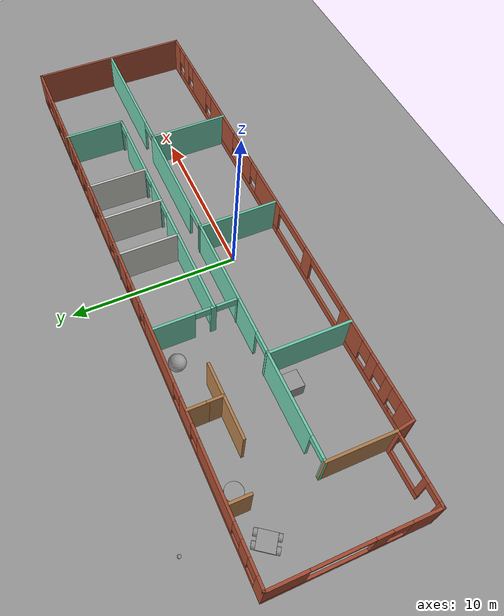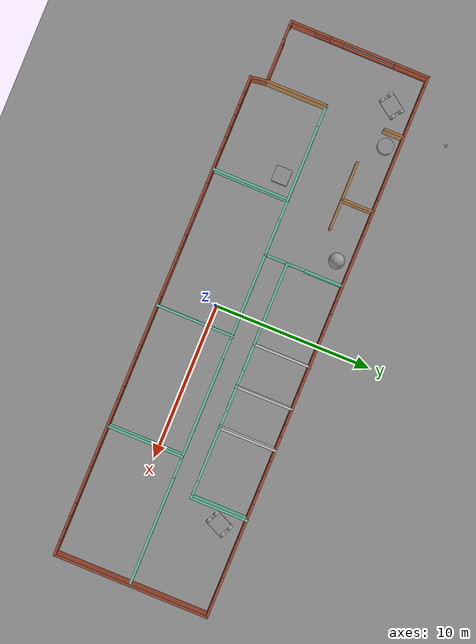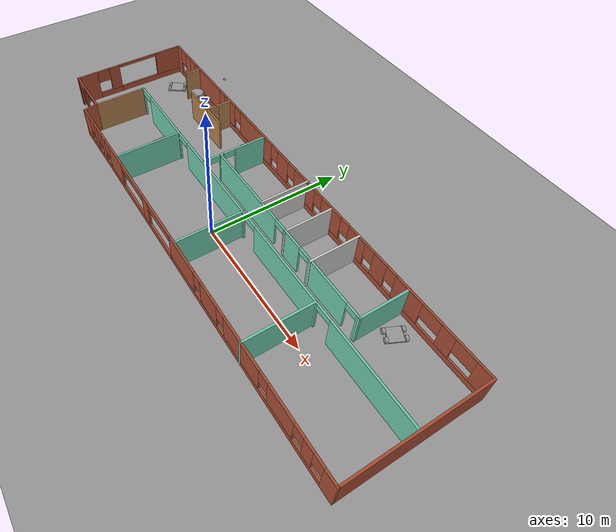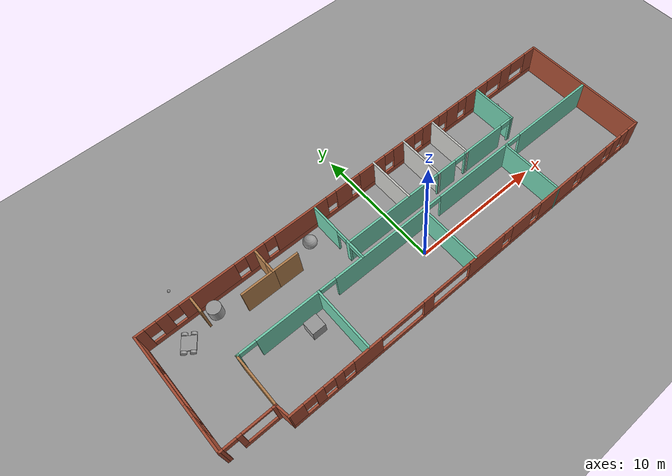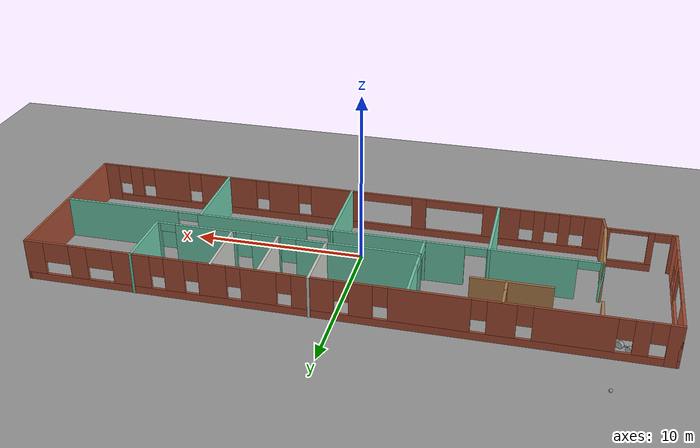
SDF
<sdf version="1.6">
 <world name="default">
  <plugin name="welcome_message" filename="libwelcome_message.so"/>
  <light name="sun" type="directional">
   <pose>0 0 10 0 -0 0</pose>
   <diffuse>0.8 0.8 0.8 1</diffuse>
   <specular>0.2 0.2 0.2 1</specular>
   <attenuation>
    <range>1000</range>
    <constant>0.9</constant>
    <linear>0.01</linear>
    <quadratic>0.001</quadratic>
   </attenuation>
   <direction>-0.5 0.1 -0.9</direction>
  </light>
  <model name="ground_plane">
   <static>1</static>
   <link name="link">
    <collision name="collision">
     <geometry><plane><normal>0 0 1</normal><size>100 100</size></plane></geometry>
     <surface><friction><ode><mu>100</mu><mu2>50</mu2></ode></friction></surface>
    </collision>
    <visual name="visual">
     <cast_shadows>0</cast_shadows>
     <geometry><plane><normal>0 0 1</normal><size>100 100</size></plane></geometry>
     <material>
      <script><uri>file://media/materials/scripts/gazebo.material</uri><name>Gazebo/Grey</name></script>
     </material>
    </visual>
   </link>
  </model>
  <gravity>0 0 -9.8</gravity>
  <magnetic_field>6e-06 2.3e-05 -4.2e-05</magnetic_field>
  <atmosphere type="adiabatic"/>
  <physics name="default_physics" default="0" type="ode">
   <max_step_size>0.001</max_step_size>
   <real_time_factor>1</real_time_factor>
   <real_time_update_rate>1000</real_time_update_rate>
  </physics>
  <scene><ambient>0.4 0.4 0.4 1</ambient><background>0.7 0.7 0.7 1</background><shadows>1</shadows></scene>
  <spherical_coordinates>
   <surface_model>EARTH_WGS84</surface_model>
   <latitude_deg>0</latitude_deg>
   <longitude_deg>0</longitude_deg>
   <elevation>0</elevation>
   <heading_deg>0</heading_deg>
  </spherical_coordinates>
  <model name="robot_model">
   <link name="link_0">
    <pose>0.018153 -0.576112 0.2 0 -0 0</pose>
    <inertial>
     <mass>1</mass>
     <inertia>
      <ixx>0.166667</ixx>
      <ixy>0</ixy>
      <ixz>0</ixz>
      <iyy>0.166667</iyy>
      <iyz>0</iyz>
      <izz>0.166667</izz>
     </inertia>
    </inertial>
    <visual name="visual">
     <geometry><box><size>1 1 0.1</size></box></geometry>
     <material>
      <lighting>1</lighting>
      <script><uri>file://media/materials/scripts/gazebo.material</uri><name>Gazebo/Grey</name></script>
      <shader type="pixel"><normal_map>__default__</normal_map></shader>
      <ambient>0.3 0.3 0.3 1</ambient>
      <diffuse>0.7 0.7 0.7 1</diffuse>
      <specular>0.01 0.01 0.01 1</specular>
      <emissive>0 0 0 1</emissive>
     </material>
    </visual>
    <collision name="collision">
     <geometry><box><size>1 1 0.1</size></box></geometry>
     <surface>
      <friction>
       <ode><mu>1</mu><mu2>1</mu2><fdir1>0 0 0</fdir1><slip1>0</slip1><slip2>0</slip2></ode>
       <torsional>
        <coefficient>1</coefficient>
        <patch_radius>0</patch_radius>
        <surface_radius>0</surface_radius>
        <use_patch_radius>1</use_patch_radius>
        <ode><slip>0</slip></ode>
       </torsional>
      </friction>
      <bounce><restitution_coefficient>0</restitution_coefficient><threshold>1e+06</threshold></bounce>
      <contact>
       <collide_without_contact>0</collide_without_contact>
       <collide_without_contact_bitmask>1</collide_without_contact_bitmask>
       <collide_bitmask>1</collide_bitmask>
       <ode>
        <soft_cfm>0</soft_cfm>
        <soft_erp>0.2</soft_erp>
        <kp>1e+13</kp>
        <kd>1</kd>
        <max_vel>0.01</max_vel>
        <min_depth>0</min_depth>
       </ode>
       <bullet>
        <split_impulse>1</split_impulse>
        <split_impulse_penetration_threshold>-0.01</split_impulse_penetration_threshold>
        <soft_cfm>0</soft_cfm>
        <soft_erp>0.2</soft_erp>
        <kp>1e+13</kp>
        <kd>1</kd>
       </bullet>
      </contact>
     </surface>
    </collision>
   </link>
   <link name="link_1">
    <pose>0.318153 -1.17613 0.2 1.5707 -0 0</pose>
    <inertial>
     <mass>1</mass>
     <inertia><ixx>0.145833</ixx><ixy>0</ixy><ixz>0</ixz><iyy>0.145833</iyy><iyz>0</iyz><izz>0.125</izz></inertia>
    </inertial>
    <visual name="visual">
     <geometry><cylinder><radius>0.2</radius><length>0.2</length></cylinder></geometry>
     <material>
      <lighting>1</lighting>
      <script><uri>file://media/materials/scripts/gazebo.material</uri><name>Gazebo/Grey</name></script>
      <shader type="pixel"><normal_map>__default__</normal_map></shader>
      <ambient>0.3 0.3 0.3 1</ambient>
      <diffuse>0.7 0.7 0.7 1</diffuse>
      <specular>0.01 0.01 0.01 1</specular>
      <emissive>0 0 0 1</emissive>
     </material>
    </visual>
    <collision name="collision">
     <geometry><cylinder><radius>0.2</radius><length>0.2</length></cylinder></geometry>
     <surface>
      <friction>
       <ode><mu>1</mu><mu2>1</mu2><fdir1>0 0 0</fdir1><slip1>0</slip1><slip2>0</slip2></ode>
       <torsional>
        <coefficient>1</coefficient>
        <patch_radius>0</patch_radius>
        <surface_radius>0</surface_radius>
        <use_patch_radius>1</use_patch_radius>
        <ode><slip>0</slip></ode>
       </torsional>
      </friction>
      <bounce><restitution_coefficient>0</restitution_coefficient><threshold>1e+06</threshold></bounce>
      <contact>
       <collide_without_contact>0</collide_without_contact>
       <collide_without_contact_bitmask>1</collide_without_contact_bitmask>
       <collide_bitmask>1</collide_bitmask>
       <ode>
        <soft_cfm>0</soft_cfm>
        <soft_erp>0.2</soft_erp>
        <kp>1e+13</kp>
        <kd>1</kd>
        <max_vel>0.01</max_vel>
        <min_depth>0</min_depth>
       </ode>
       <bullet>
        <split_impulse>1</split_impulse>
        <split_impulse_penetration_threshold>-0.01</split_impulse_penetration_threshold>
        <soft_cfm>0</soft_cfm>
        <soft_erp>0.2</soft_erp>
        <kp>1e+13</kp>
        <kd>1</kd>
       </bullet>
      </contact>
     </surface>
    </collision>
   </link>
   <link name="link_1_clone">
    <pose>-0.281847 -1.17613 0.2 1.5707 -0 0</pose>
    <inertial>
     <mass>1</mass>
     <inertia><ixx>0.145833</ixx><ixy>0</ixy><ixz>0</ixz><iyy>0.145833</iyy><iyz>0</iyz><izz>0.125</izz></inertia>
    </inertial>
    <visual name="visual">
     <geometry><cylinder><radius>0.2</radius><length>0.2</length></cylinder></geometry>
     <material>
      <lighting>1</lighting>
      <script><uri>file://media/materials/scripts/gazebo.material</uri><name>Gazebo/Grey</name></script>
      <shader type="pixel"><normal_map>__default__</normal_map></shader>
      <ambient>0.3 0.3 0.3 1</ambient>
      <diffuse>0.7 0.7 0.7 1</diffuse>
      <specular>0.01 0.01 0.01 1</specular>
      <emissive>0 0 0 1</emissive>
     </material>
    </visual>
    <collision name="collision">
     <geometry><cylinder><radius>0.2</radius><length>0.2</length></cylinder></geometry>
     <surface>
      <friction>
       <ode><mu>1</mu><mu2>1</mu2><fdir1>0 0 0</fdir1><slip1>0</slip1><slip2>0</slip2></ode>
       <torsional>
        <coefficient>1</coefficient>
        <patch_radius>0</patch_radius>
        <surface_radius>0</surface_radius>
        <use_patch_radius>1</use_patch_radius>
        <ode><slip>0</slip></ode>
       </torsional>
      </friction>
      <bounce><restitution_coefficient>0</restitution_coefficient><threshold>1e+06</threshold></bounce>
      <contact>
       <collide_without_contact>0</collide_without_contact>
       <collide_without_contact_bitmask>1</collide_without_contact_bitmask>
       <collide_bitmask>1</collide_bitmask>
       <ode>
        <soft_cfm>0</soft_cfm>
        <soft_erp>0.2</soft_erp>
        <kp>1e+13</kp>
        <kd>1</kd>
        <max_vel>0.01</max_vel>
        <min_depth>0</min_depth>
       </ode>
       <bullet>
        <split_impulse>1</split_impulse>
        <split_impulse_penetration_threshold>-0.01</split_impulse_penetration_threshold>
        <soft_cfm>0</soft_cfm>
        <soft_erp>0.2</soft_erp>
        <kp>1e+13</kp>
        <kd>1</kd>
       </bullet>
      </contact>
     </surface>
    </collision>
   </link>
   <link name="link_1_clone_clone">
    <pose>-0.281847 0.023907 0.2 1.5707 -0 0</pose>
    <inertial>
     <mass>1</mass>
     <inertia><ixx>0.145833</ixx><ixy>0</ixy><ixz>0</ixz><iyy>0.145833</iyy><iyz>0</iyz><izz>0.125</izz></inertia>
    </inertial>
    <visual name="visual">
     <geometry><cylinder><radius>0.2</radius><length>0.2</length></cylinder></geometry>
     <material>
      <lighting>1</lighting>
      <script><uri>file://media/materials/scripts/gazebo.material</uri><name>Gazebo/Grey</name></script>
      <shader type="pixel"><normal_map>__default__</normal_map></shader>
      <ambient>0.3 0.3 0.3 1</ambient>
      <diffuse>0.7 0.7 0.7 1</diffuse>
      <specular>0.01 0.01 0.01 1</specular>
      <emissive>0 0 0 1</emissive>
     </material>
    </visual>
    <collision name="collision">
     <geometry><cylinder><radius>0.2</radius><length>0.2</length></cylinder></geometry>
     <surface>
      <friction>
       <ode><mu>1</mu><mu2>1</mu2><fdir1>0 0 0</fdir1><slip1>0</slip1><slip2>0</slip2></ode>
       <torsional>
        <coefficient>1</coefficient>
        <patch_radius>0</patch_radius>
        <surface_radius>0</surface_radius>
        <use_patch_radius>1</use_patch_radius>
        <ode><slip>0</slip></ode>
       </torsional>
      </friction>
      <bounce><restitution_coefficient>0</restitution_coefficient><threshold>1e+06</threshold></bounce>
      <contact>
       <collide_without_contact>0</collide_without_contact>
       <collide_without_contact_bitmask>1</collide_without_contact_bitmask>
       <collide_bitmask>1</collide_bitmask>
       <ode>
        <soft_cfm>0</soft_cfm>
        <soft_erp>0.2</soft_erp>
        <kp>1e+13</kp>
        <kd>1</kd>
        <max_vel>0.01</max_vel>
        <min_depth>0</min_depth>
       </ode>
       <bullet>
        <split_impulse>1</split_impulse>
        <split_impulse_penetration_threshold>-0.01</split_impulse_penetration_threshold>
        <soft_cfm>0</soft_cfm>
        <soft_erp>0.2</soft_erp>
        <kp>1e+13</kp>
        <kd>1</kd>
       </bullet>
      </contact>
     </surface>
    </collision>
   </link>
   <link name="link_1_clone_clone_0">
    <pose>0.318153 0.023907 0.2 1.5707 -0 0</pose>
    <inertial>
     <mass>1</mass>
     <inertia><ixx>0.145833</ixx><ixy>0</ixy><ixz>0</ixz><iyy>0.145833</iyy><iyz>0</iyz><izz>0.125</izz></inertia>
    </inertial>
    <visual name="visual">
     <geometry><cylinder><radius>0.2</radius><length>0.2</length></cylinder></geometry>
     <material>
      <lighting>1</lighting>
      <script><uri>file://media/materials/scripts/gazebo.material</uri><name>Gazebo/Grey</name></script>
      <shader type="pixel"><normal_map>__default__</normal_map></shader>
      <ambient>0.3 0.3 0.3 1</ambient>
      <diffuse>0.7 0.7 0.7 1</diffuse>
      <specular>0.01 0.01 0.01 1</specular>
      <emissive>0 0 0 1</emissive>
     </material>
    </visual>
    <collision name="collision">
     <geometry><cylinder><radius>0.2</radius><length>0.2</length></cylinder></geometry>
     <surface>
      <friction>
       <ode><mu>1</mu><mu2>1</mu2><fdir1>0 0 0</fdir1><slip1>0</slip1><slip2>0</slip2></ode>
       <torsional>
        <coefficient>1</coefficient>
        <patch_radius>0</patch_radius>
        <surface_radius>0</surface_radius>
        <use_patch_radius>1</use_patch_radius>
        <ode><slip>0</slip></ode>
       </torsional>
      </friction>
      <bounce><restitution_coefficient>0</restitution_coefficient><threshold>1e+06</threshold></bounce>
      <contact>
       <collide_without_contact>0</collide_without_contact>
       <collide_without_contact_bitmask>1</collide_without_contact_bitmask>
       <collide_bitmask>1</collide_bitmask>
       <ode>
        <soft_cfm>0</soft_cfm>
        <soft_erp>0.2</soft_erp>
        <kp>1e+13</kp>
        <kd>1</kd>
        <max_vel>0.01</max_vel>
        <min_depth>0</min_depth>
       </ode>
       <bullet>
        <split_impulse>1</split_impulse>
        <split_impulse_penetration_threshold>-0.01</split_impulse_penetration_threshold>
        <soft_cfm>0</soft_cfm>
        <soft_erp>0.2</soft_erp>
        <kp>1e+13</kp>
        <kd>1</kd>
       </bullet>
      </contact>
     </surface>
    </collision>
   </link>
   <joint name="link_0_JOINT_0" type="revolute">
    <parent>link_0</parent>
    <child>link_1_clone</child>
    <axis>
     <xyz>0 0 1</xyz>
     <use_parent_model_frame>0</use_parent_model_frame>
     <limit>
      <lower>-1.79769e+308</lower>
      <upper>1.79769e+308</upper>
      <effort>-1</effort>
      <velocity>-1</velocity>
     </limit>
     <dynamics>
      <spring_reference>0</spring_reference>
      <spring_stiffness>0</spring_stiffness>
      <damping>0</damping>
     </dynamics>
    </axis>
    <physics>
     <ode><limit><cfm>0</cfm><erp>0.2</erp></limit><suspension><cfm>0</cfm><erp>0.2</erp></suspension></ode>
    </physics>
   </joint>
   <joint name="link_0_JOINT_1" type="revolute">
    <parent>link_0</parent>
    <child>link_1</child>
    <axis>
     <xyz>0 0 1</xyz>
     <use_parent_model_frame>0</use_parent_model_frame>
     <limit>
      <lower>-1.79769e+308</lower>
      <upper>1.79769e+308</upper>
      <effort>-1</effort>
      <velocity>-1</velocity>
     </limit>
     <dynamics>
      <spring_reference>0</spring_reference>
      <spring_stiffness>0</spring_stiffness>
      <damping>0</damping>
     </dynamics>
    </axis>
    <physics>
     <ode><limit><cfm>0</cfm><erp>0.2</erp></limit><suspension><cfm>0</cfm><erp>0.2</erp></suspension></ode>
    </physics>
   </joint>
   <joint name="link_0_JOINT_2" type="revolute">
    <parent>link_0</parent>
    <child>link_1_clone_clone</child>
    <axis>
     <xyz>0 0 1</xyz>
     <use_parent_model_frame>0</use_parent_model_frame>
     <limit>
      <lower>-1.79769e+308</lower>
      <upper>1.79769e+308</upper>
      <effort>-1</effort>
      <velocity>-1</velocity>
     </limit>
     <dynamics>
      <spring_reference>0</spring_reference>
      <spring_stiffness>0</spring_stiffness>
      <damping>0</damping>
     </dynamics>
    </axis>
    <physics>
     <ode><limit><cfm>0</cfm><erp>0.2</erp></limit><suspension><cfm>0</cfm><erp>0.2</erp></suspension></ode>
    </physics>
   </joint>
   <joint name="link_0_JOINT_3" type="revolute">
    <parent>link_0</parent>
    <child>link_1_clone_clone_0</child>
    <axis>
     <xyz>0 0 1</xyz>
     <use_parent_model_frame>0</use_parent_model_frame>
     <limit>
      <lower>-1.79769e+308</lower>
      <upper>1.79769e+308</upper>
      <effort>-1</effort>
      <velocity>-1</velocity>
     </limit>
     <dynamics>
      <spring_reference>0</spring_reference>
      <spring_stiffness>0</spring_stiffness>
      <damping>0</damping>
     </dynamics>
    </axis>
    <physics>
     <ode><limit><cfm>0</cfm><erp>0.2</erp></limit><suspension><cfm>0</cfm><erp>0.2</erp></suspension></ode>
    </physics>
   </joint>
   <static>0</static>
   <pose>12.4164 5.72179 4e-06 -5e-06 0 -0.433048</pose>
  </model>
  <model name="building_model">
   <pose>0.0184 1.65847 0 0 -0 0</pose>
   <link name="Wall_1">
    <pose>-15.5 -3.93769 0 0 -0 3.14159</pose>
    <visual name="Wall_1_Visual_0">
     <pose>-1.82542 0 1.25 0 -0 0</pose>
     <geometry><box><size>0.349165 0.15 2.5</size></box></geometry>
     <material>
      <script><uri>file://media/materials/scripts/gazebo.material</uri><name>Gazebo/Bricks</name></script>
      <ambient>1 1 1 1</ambient>
     </material>
     <meta><layer>0</layer></meta>
    </visual>
    <collision name="Wall_1_Collision_0">
     <geometry><box><size>0.349165 0.15 2.5</size></box></geometry>
     <pose>-1.82542 0 1.25 0 -0 0</pose>
    </collision>
    <visual name="Wall_1_Visual_1">
     <pose>1.83136 0 1.25 0 -0 0</pose>
     <geometry><box><size>0.337283 0.15 2.5</size></box></geometry>
     <material>
      <script><uri>file://media/materials/scripts/gazebo.material</uri><name>Gazebo/Bricks</name></script>
      <ambient>1 1 1 1</ambient>
     </material>
     <meta><layer>0</layer></meta>
    </visual>
    <collision name="Wall_1_Collision_1">
     <geometry><box><size>0.337283 0.15 2.5</size></box></geometry>
     <pose>1.83136 0 1.25 0 -0 0</pose>
    </collision>
    <visual name="Wall_1_Visual_2">
     <pose>-0.444059 0 0.25 0 -0 0</pose>
     <geometry><box><size>2.41355 0.15 0.5</size></box></geometry>
     <material>
      <script><uri>file://media/materials/scripts/gazebo.material</uri><name>Gazebo/Bricks</name></script>
      <ambient>1 1 1 1</ambient>
     </material>
     <meta><layer>0</layer></meta>
    </visual>
    <collision name="Wall_1_Collision_2">
     <geometry><box><size>2.41355 0.15 0.5</size></box></geometry>
     <pose>-0.444059 0 0.25 0 -0 0</pose>
    </collision>
    <visual name="Wall_1_Visual_3">
     <pose>0.594441 0 1.5 0 -0 0</pose>
     <geometry><box><size>0.336552 0.15 2</size></box></geometry>
     <material>
      <script><uri>file://media/materials/scripts/gazebo.material</uri><name>Gazebo/Bricks</name></script>
      <ambient>1 1 1 1</ambient>
     </material>
     <meta><layer>0</layer></meta>
    </visual>
    <collision name="Wall_1_Collision_3">
     <geometry><box><size>0.336552 0.15 2</size></box></geometry>
     <pose>0.594441 0 1.5 0 -0 0</pose>
    </collision>
    <visual name="Wall_1_Visual_4">
     <pose>1.21272 0 2.25 0 -0 0</pose>
     <geometry><box><size>0.9 0.15 0.5</size></box></geometry>
     <material>
      <script><uri>file://media/materials/scripts/gazebo.material</uri><name>Gazebo/Bricks</name></script>
      <ambient>1 1 1 1</ambient>
     </material>
     <meta><layer>0</layer></meta>
    </visual>
    <collision name="Wall_1_Collision_4">
     <geometry><box><size>0.9 0.15 0.5</size></box></geometry>
     <pose>1.21272 0 2.25 0 -0 0</pose>
    </collision>
    <visual name="Wall_1_Visual_5">
     <pose>-0.612335 0 2.4 0 -0 0</pose>
     <geometry><box><size>2.077 0.15 0.2</size></box></geometry>
     <material>
      <script><uri>file://media/materials/scripts/gazebo.material</uri><name>Gazebo/Bricks</name></script>
      <ambient>1 1 1 1</ambient>
     </material>
     <meta><layer>0</layer></meta>
    </visual>
    <collision name="Wall_1_Collision_5">
     <geometry><box><size>2.077 0.15 0.2</size></box></geometry>
     <pose>-0.612335 0 2.4 0 -0 0</pose>
    </collision>
   </link>
   <link name="Wall_10">
    <pose>1.85 -0.087691 0 0 -0 0</pose>
    <visual name="Wall_10_Visual_0">
     <pose>-15.3838 0 1.25 0 -0 0</pose>
     <geometry><box><size>0.232456 0.15 2.5</size></box></geometry>
     <material>
      <script><uri>file://media/materials/scripts/gazebo.material</uri><name>Gazebo/Grey</name></script>
      <ambient>0.435294 0.796078 0.67451 1</ambient>
     </material>
     <meta><layer>0</layer></meta>
    </visual>
    <collision name="Wall_10_Collision_0">
     <geometry><box><size>0.232456 0.15 2.5</size></box></geometry>
     <pose>-15.3838 0 1.25 0 -0 0</pose>
    </collision>
    <visual name="Wall_10_Visual_1">
     <pose>-11.6471 0 1.25 0 -0 0</pose>
     <geometry><box><size>4.84093 0.15 2.5</size></box></geometry>
     <material>
      <script><uri>file://media/materials/scripts/gazebo.material</uri><name>Gazebo/Grey</name></script>
      <ambient>0.435294 0.796078 0.67451 1</ambient>
     </material>
     <meta><layer>0</layer></meta>
    </visual>
    <collision name="Wall_10_Collision_1">
     <geometry><box><size>4.84093 0.15 2.5</size></box></geometry>
     <pose>-11.6471 0 1.25 0 -0 0</pose>
    </collision>
    <visual name="Wall_10_Visual_2">
     <pose>-4.17733 0 1.25 0 -0 0</pose>
     <geometry><box><size>7.69857 0.15 2.5</size></box></geometry>
     <material>
      <script><uri>file://media/materials/scripts/gazebo.material</uri><name>Gazebo/Grey</name></script>
      <ambient>0.435294 0.796078 0.67451 1</ambient>
     </material>
     <meta><layer>0</layer></meta>
    </visual>
    <collision name="Wall_10_Collision_2">
     <geometry><box><size>7.69857 0.15 2.5</size></box></geometry>
     <pose>-4.17733 0 1.25 0 -0 0</pose>
    </collision>
    <visual name="Wall_10_Visual_3">
     <pose>4.17858 0 1.25 0 -0 0</pose>
     <geometry><box><size>6.51326 0.15 2.5</size></box></geometry>
     <material>
      <script><uri>file://media/materials/scripts/gazebo.material</uri><name>Gazebo/Grey</name></script>
      <ambient>0.435294 0.796078 0.67451 1</ambient>
     </material>
     <meta><layer>0</layer></meta>
    </visual>
    <collision name="Wall_10_Collision_3">
     <geometry><box><size>6.51326 0.15 2.5</size></box></geometry>
     <pose>4.17858 0 1.25 0 -0 0</pose>
    </collision>
    <visual name="Wall_10_Visual_4">
     <pose>12.0676 0 1.25 0 -0 0</pose>
     <geometry><box><size>6.86479 0.15 2.5</size></box></geometry>
     <material>
      <script><uri>file://media/materials/scripts/gazebo.material</uri><name>Gazebo/Grey</name></script>
      <ambient>0.435294 0.796078 0.67451 1</ambient>
     </material>
     <meta><layer>0</layer></meta>
    </visual>
    <collision name="Wall_10_Collision_4">
     <geometry><box><size>6.86479 0.15 2.5</size></box></geometry>
     <pose>12.0676 0 1.25 0 -0 0</pose>
    </collision>
    <visual name="Wall_10_Visual_5">
     <pose>-14.6675 0 2.25 0 -0 0</pose>
     <geometry><box><size>1.2 0.15 0.5</size></box></geometry>
     <material>
      <script><uri>file://media/materials/scripts/gazebo.material</uri><name>Gazebo/Grey</name></script>
      <ambient>0.435294 0.796078 0.67451 1</ambient>
     </material>
     <meta><layer>0</layer></meta>
    </visual>
    <collision name="Wall_10_Collision_5">
     <geometry><box><size>1.2 0.15 0.5</size></box></geometry>
     <pose>-14.6675 0 2.25 0 -0 0</pose>
    </collision>
    <visual name="Wall_10_Visual_6">
     <pose>-8.62661 0 2.25 0 -0 0</pose>
     <geometry><box><size>1.2 0.15 0.5</size></box></geometry>
     <material>
      <script><uri>file://media/materials/scripts/gazebo.material</uri><name>Gazebo/Grey</name></script>
      <ambient>0.435294 0.796078 0.67451 1</ambient>
     </material>
     <meta><layer>0</layer></meta>
    </visual>
    <collision name="Wall_10_Collision_6">
     <geometry><box><size>1.2 0.15 0.5</size></box></geometry>
     <pose>-8.62661 0 2.25 0 -0 0</pose>
    </collision>
    <visual name="Wall_10_Visual_7">
     <pose>0.296954 0 2.25 0 -0 0</pose>
     <geometry><box><size>1.25 0.15 0.5</size></box></geometry>
     <material>
      <script><uri>file://media/materials/scripts/gazebo.material</uri><name>Gazebo/Grey</name></script>
      <ambient>0.435294 0.796078 0.67451 1</ambient>
     </material>
     <meta><layer>0</layer></meta>
    </visual>
    <collision name="Wall_10_Collision_7">
     <geometry><box><size>1.25 0.15 0.5</size></box></geometry>
     <pose>0.296954 0 2.25 0 -0 0</pose>
    </collision>
    <visual name="Wall_10_Visual_8">
     <pose>8.03521 0 2.25 0 -0 0</pose>
     <geometry><box><size>1.2 0.15 0.5</size></box></geometry>
     <material>
      <script><uri>file://media/materials/scripts/gazebo.material</uri><name>Gazebo/Grey</name></script>
      <ambient>0.435294 0.796078 0.67451 1</ambient>
     </material>
     <meta><layer>0</layer></meta>
    </visual>
    <collision name="Wall_10_Collision_8">
     <geometry><box><size>1.2 0.15 0.5</size></box></geometry>
     <pose>8.03521 0 2.25 0 -0 0</pose>
    </collision>
   </link>
   <link name="Wall_12">
    <collision name="Wall_12_Collision">
     <geometry><box><size>1.25 0.15 2.5</size></box></geometry>
     <pose>0 0 1.25 0 -0 0</pose>
    </collision>
    <visual name="Wall_12_Visual">
     <pose>0 0 1.25 0 -0 0</pose>
     <geometry><box><size>1.25 0.15 2.5</size></box></geometry>
     <material>
      <script><uri>file://media/materials/scripts/gazebo.material</uri><name>Gazebo/Wood</name></script>
      <ambient>1 1 1 1</ambient>
     </material>
     <meta><layer>0</layer></meta>
    </visual>
    <pose>-13.575 4.25547 0 0 -0 1.5708</pose>
   </link>
   <link name="Wall_14">
    <collision name="Wall_14_Collision">
     <geometry><box><size>1.25 0.15 2.5</size></box></geometry>
     <pose>0 0 1.25 0 -0 0</pose>
    </collision>
    <visual name="Wall_14_Visual">
     <pose>0 0 1.25 0 -0 0</pose>
     <geometry><box><size>1.25 0.15 2.5</size></box></geometry>
     <material>
      <script><uri>file://media/materials/scripts/gazebo.material</uri><name>Gazebo/Wood</name></script>
      <ambient>1 1 1 1</ambient>
     </material>
     <meta><layer>0</layer></meta>
    </visual>
    <pose>-8.74774 4.32205 0 0 0 -1.5708</pose>
   </link>
   <link name="Wall_15">
    <collision name="Wall_15_Collision">
     <geometry><box><size>1 0.15 2.5</size></box></geometry>
     <pose>0 0 1.25 0 -0 0</pose>
    </collision>
    <visual name="Wall_15_Visual">
     <pose>0 0 1.25 0 -0 0</pose>
     <geometry><box><size>1 0.15 2.5</size></box></geometry>
     <material>
      <script><uri>file://media/materials/scripts/gazebo.material</uri><name>Gazebo/Wood</name></script>
      <ambient>1 1 1 1</ambient>
     </material>
     <meta><layer>0</layer></meta>
    </visual>
    <pose>-8.74774 3.34705 0 0 0 -1.5708</pose>
   </link>
   <link name="Wall_16">
    <collision name="Wall_16_Collision">
     <geometry><box><size>2.5 0.15 2.5</size></box></geometry>
     <pose>0 0 1.25 0 -0 0</pose>
    </collision>
    <visual name="Wall_16_Visual">
     <pose>0 0 1.25 0 -0 0</pose>
     <geometry><box><size>2.5 0.15 2.5</size></box></geometry>
     <material>
      <script><uri>file://media/materials/scripts/gazebo.material</uri><name>Gazebo/Wood</name></script>
      <ambient>1 1 1 1</ambient>
     </material>
     <meta><layer>0</layer></meta>
    </visual>
    <pose>-9.92274 2.92205 0 0 -0 3.14159</pose>
   </link>
   <link name="Wall_18">
    <collision name="Wall_18_Collision">
     <geometry><box><size>2 0.15 2.5</size></box></geometry>
     <pose>0 0 1.25 0 -0 0</pose>
    </collision>
    <visual name="Wall_18_Visual">
     <pose>0 0 1.25 0 -0 0</pose>
     <geometry><box><size>2 0.15 2.5</size></box></geometry>
     <material>
      <script><uri>file://media/materials/scripts/gazebo.material</uri><name>Gazebo/Wood</name></script>
      <ambient>1 1 1 1</ambient>
     </material>
     <meta><layer>0</layer></meta>
    </visual>
    <pose>-7.82274 2.92205 0 0 -0 0</pose>
   </link>
   <link name="Wall_20">
    <pose>-3.9406 2.34911 0 0 -0 1.5708</pose>
    <visual name="Wall_20_Visual_0">
     <pose>-2.41051 0 1.25 0 -0 0</pose>
     <geometry><box><size>0.178975 0.15 2.5</size></box></geometry>
     <material>
      <script><uri>file://media/materials/scripts/gazebo.material</uri><name>Gazebo/Grey</name></script>
      <ambient>0.435294 0.796078 0.67451 1</ambient>
     </material>
     <meta><layer>0</layer></meta>
    </visual>
    <collision name="Wall_20_Collision_0">
     <geometry><box><size>0.178975 0.15 2.5</size></box></geometry>
     <pose>-2.41051 0 1.25 0 -0 0</pose>
    </collision>
    <visual name="Wall_20_Visual_1">
     <pose>-0.958717 0 1.25 0 -0 0</pose>
     <geometry><box><size>0.324616 0.15 2.5</size></box></geometry>
     <material>
      <script><uri>file://media/materials/scripts/gazebo.material</uri><name>Gazebo/Grey</name></script>
      <ambient>0.435294 0.796078 0.67451 1</ambient>
     </material>
     <meta><layer>0</layer></meta>
    </visual>
    <collision name="Wall_20_Collision_1">
     <geometry><box><size>0.324616 0.15 2.5</size></box></geometry>
     <pose>-0.958717 0 1.25 0 -0 0</pose>
    </collision>
    <visual name="Wall_20_Visual_2">
     <pose>1.3018 0 1.25 0 -0 0</pose>
     <geometry><box><size>2.39641 0.15 2.5</size></box></geometry>
     <material>
      <script><uri>file://media/materials/scripts/gazebo.material</uri><name>Gazebo/Grey</name></script>
      <ambient>0.435294 0.796078 0.67451 1</ambient>
     </material>
     <meta><layer>0</layer></meta>
    </visual>
    <collision name="Wall_20_Collision_2">
     <geometry><box><size>2.39641 0.15 2.5</size></box></geometry>
     <pose>1.3018 0 1.25 0 -0 0</pose>
    </collision>
    <visual name="Wall_20_Visual_3">
     <pose>-1.72103 0 2.25 0 -0 0</pose>
     <geometry><box><size>1.2 0.15 0.5</size></box></geometry>
     <material>
      <script><uri>file://media/materials/scripts/gazebo.material</uri><name>Gazebo/Grey</name></script>
      <ambient>0.435294 0.796078 0.67451 1</ambient>
     </material>
     <meta><layer>0</layer></meta>
    </visual>
    <collision name="Wall_20_Collision_3">
     <geometry><box><size>1.2 0.15 0.5</size></box></geometry>
     <pose>-1.72103 0 2.25 0 -0 0</pose>
    </collision>
    <visual name="Wall_20_Visual_4">
     <pose>-0.346409 0 2.25 0 -0 0</pose>
     <geometry><box><size>0.9 0.15 0.5</size></box></geometry>
     <material>
      <script><uri>file://media/materials/scripts/gazebo.material</uri><name>Gazebo/Grey</name></script>
      <ambient>0.435294 0.796078 0.67451 1</ambient>
     </material>
     <meta><layer>0</layer></meta>
    </visual>
    <collision name="Wall_20_Collision_4">
     <geometry><box><size>0.9 0.15 0.5</size></box></geometry>
     <pose>-0.346409 0 2.25 0 -0 0</pose>
    </collision>
   </link>
   <link name="Wall_22">
    <collision name="Wall_22_Collision">
     <geometry><box><size>5 0.15 2.5</size></box></geometry>
     <pose>0 0 1.25 0 -0 0</pose>
    </collision>
    <visual name="Wall_22_Visual">
     <pose>0 0 1.25 0 -0 0</pose>
     <geometry><box><size>5 0.15 2.5</size></box></geometry>
     <material>
      <script><uri>file://media/materials/scripts/gazebo.material</uri><name>Gazebo/Grey</name></script>
      <ambient>0.435294 0.796078 0.67451 1</ambient>
     </material>
     <meta><layer>0</layer></meta>
    </visual>
    <pose>-7.5007 -2.50088 0 0 0 -1.5708</pose>
   </link>
   <link name="Wall_24">
    <pose>3.62951 1.33207 0 0 -0 0</pose>
    <visual name="Wall_24_Visual_0">
     <pose>-4.14379 0 1.25 0 -0 0</pose>
     <geometry><box><size>6.96242 0.15 2.5</size></box></geometry>
     <material>
      <script><uri>file://media/materials/scripts/gazebo.material</uri><name>Gazebo/Grey</name></script>
      <ambient>0.435294 0.796078 0.67451 1</ambient>
     </material>
     <meta><layer>0</layer></meta>
    </visual>
    <collision name="Wall_24_Collision_0">
     <geometry><box><size>6.96242 0.15 2.5</size></box></geometry>
     <pose>-4.14379 0 1.25 0 -0 0</pose>
    </collision>
    <visual name="Wall_24_Visual_1">
     <pose>1.07877 0 1.25 0 -0 0</pose>
     <geometry><box><size>1.6827 0.15 2.5</size></box></geometry>
     <material>
      <script><uri>file://media/materials/scripts/gazebo.material</uri><name>Gazebo/Grey</name></script>
      <ambient>0.435294 0.796078 0.67451 1</ambient>
     </material>
     <meta><layer>0</layer></meta>
    </visual>
    <collision name="Wall_24_Collision_1">
     <geometry><box><size>1.6827 0.15 2.5</size></box></geometry>
     <pose>1.07877 0 1.25 0 -0 0</pose>
    </collision>
    <visual name="Wall_24_Visual_2">
     <pose>4.62999 0 1.25 0 -0 0</pose>
     <geometry><box><size>3.61973 0.15 2.5</size></box></geometry>
     <material>
      <script><uri>file://media/materials/scripts/gazebo.material</uri><name>Gazebo/Grey</name></script>
      <ambient>0.435294 0.796078 0.67451 1</ambient>
     </material>
     <meta><layer>0</layer></meta>
    </visual>
    <collision name="Wall_24_Collision_2">
     <geometry><box><size>3.61973 0.15 2.5</size></box></geometry>
     <pose>4.62999 0 1.25 0 -0 0</pose>
    </collision>
    <visual name="Wall_24_Visual_3">
     <pose>7.48243 0 1.25 0 -0 0</pose>
     <geometry><box><size>0.285144 0.15 2.5</size></box></geometry>
     <material>
      <script><uri>file://media/materials/scripts/gazebo.material</uri><name>Gazebo/Grey</name></script>
      <ambient>0.435294 0.796078 0.67451 1</ambient>
     </material>
     <meta><layer>0</layer></meta>
    </visual>
    <collision name="Wall_24_Collision_3">
     <geometry><box><size>0.285144 0.15 2.5</size></box></geometry>
     <pose>7.48243 0 1.25 0 -0 0</pose>
    </collision>
    <visual name="Wall_24_Visual_4">
     <pose>-0.212578 0 2.25 0 -0 0</pose>
     <geometry><box><size>0.9 0.15 0.5</size></box></geometry>
     <material>
      <script><uri>file://media/materials/scripts/gazebo.material</uri><name>Gazebo/Grey</name></script>
      <ambient>0.435294 0.796078 0.67451 1</ambient>
     </material>
     <meta><layer>0</layer></meta>
    </visual>
    <collision name="Wall_24_Collision_4">
     <geometry><box><size>0.9 0.15 0.5</size></box></geometry>
     <pose>-0.212578 0 2.25 0 -0 0</pose>
    </collision>
    <visual name="Wall_24_Visual_5">
     <pose>2.37012 0 2.25 0 -0 0</pose>
     <geometry><box><size>0.9 0.15 0.5</size></box></geometry>
     <material>
      <script><uri>file://media/materials/scripts/gazebo.material</uri><name>Gazebo/Grey</name></script>
      <ambient>0.435294 0.796078 0.67451 1</ambient>
     </material>
     <meta><layer>0</layer></meta>
    </visual>
    <collision name="Wall_24_Collision_5">
     <geometry><box><size>0.9 0.15 0.5</size></box></geometry>
     <pose>2.37012 0 2.25 0 -0 0</pose>
    </collision>
    <visual name="Wall_24_Visual_6">
     <pose>6.88986 0 2.25 0 -0 0</pose>
     <geometry><box><size>0.9 0.15 0.5</size></box></geometry>
     <material>
      <script><uri>file://media/materials/scripts/gazebo.material</uri><name>Gazebo/Grey</name></script>
      <ambient>0.435294 0.796078 0.67451 1</ambient>
     </material>
     <meta><layer>0</layer></meta>
    </visual>
    <collision name="Wall_24_Collision_6">
     <geometry><box><size>0.9 0.15 0.5</size></box></geometry>
     <pose>6.88986 0 2.25 0 -0 0</pose>
    </collision>
   </link>
   <link name="Wall_25">
    <collision name="Wall_25_Collision">
     <geometry><box><size>3.75 0.15 2.5</size></box></geometry>
     <pose>0 0 1.25 0 -0 0</pose>
    </collision>
    <visual name="Wall_25_Visual">
     <pose>0 0 1.25 0 -0 0</pose>
     <geometry><box><size>3.75 0.15 2.5</size></box></geometry>
     <material>
      <script><uri>file://media/materials/scripts/gazebo.material</uri><name>Gazebo/Grey</name></script>
      <ambient>0.435294 0.796078 0.67451 1</ambient>
     </material>
     <meta><layer>0</layer></meta>
    </visual>
    <pose>11.1795 3.13206 0 0 -0 1.5708</pose>
   </link>
   <link name="Wall_27">
    <collision name="Wall_27_Collision">
     <geometry><box><size>3.75 0.15 2.5</size></box></geometry>
     <pose>0 0 1.25 0 -0 0</pose>
    </collision>
    <visual name="Wall_27_Visual">
     <pose>0 0 1.25 0 -0 0</pose>
     <geometry><box><size>3.75 0.15 2.5</size></box></geometry>
     <material>
      <script><uri>file://media/materials/scripts/gazebo.material</uri><name>Gazebo/CeilingTiled</name></script>
      <ambient>1 1 1 1</ambient>
     </material>
     <meta><layer>0</layer></meta>
    </visual>
    <pose>1.26882 3.15218 0 0 -0 1.5708</pose>
   </link>
   <link name="Wall_29">
    <collision name="Wall_29_Collision">
     <geometry><box><size>3.75 0.15 2.5</size></box></geometry>
     <pose>0 0 1.25 0 -0 0</pose>
    </collision>
    <visual name="Wall_29_Visual">
     <pose>0 0 1.25 0 -0 0</pose>
     <geometry><box><size>3.75 0.15 2.5</size></box></geometry>
     <material>
      <script><uri>file://media/materials/scripts/gazebo.material</uri><name>Gazebo/CeilingTiled</name></script>
      <ambient>1 1 1 1</ambient>
     </material>
     <meta><layer>0</layer></meta>
    </visual>
    <pose>6.67937 3.11195 0 0 -0 1.5708</pose>
   </link>
   <link name="Wall_31">
    <collision name="Wall_31_Collision">
     <geometry><box><size>3.75 0.15 2.5</size></box></geometry>
     <pose>0 0 1.25 0 -0 0</pose>
    </collision>
    <visual name="Wall_31_Visual">
     <pose>0 0 1.25 0 -0 0</pose>
     <geometry><box><size>3.75 0.15 2.5</size></box></geometry>
     <material>
      <script><uri>file://media/materials/scripts/gazebo.material</uri><name>Gazebo/CeilingTiled</name></script>
      <ambient>1 1 1 1</ambient>
     </material>
     <meta><layer>0</layer></meta>
    </visual>
    <pose>4.02438 3.11195 0 0 -0 1.5708</pose>
   </link>
   <link name="Wall_33">
    <collision name="Wall_33_Collision">
     <geometry><box><size>5 0.15 2.5</size></box></geometry>
     <pose>0 0 1.25 0 -0 0</pose>
    </collision>
    <visual name="Wall_33_Visual">
     <pose>0 0 1.25 0 -0 0</pose>
     <geometry><box><size>5 0.15 2.5</size></box></geometry>
     <material>
      <script><uri>file://media/materials/scripts/gazebo.material</uri><name>Gazebo/Grey</name></script>
      <ambient>0.435294 0.796078 0.67451 1</ambient>
     </material>
     <meta><layer>0</layer></meta>
    </visual>
    <pose>1.30855 -2.48092 0 0 0 -1.5708</pose>
   </link>
   <link name="Wall_35">
    <collision name="Wall_35_Collision">
     <geometry><box><size>5 0.15 2.5</size></box></geometry>
     <pose>0 0 1.25 0 -0 0</pose>
    </collision>
    <visual name="Wall_35_Visual">
     <pose>0 0 1.25 0 -0 0</pose>
     <geometry><box><size>5 0.15 2.5</size></box></geometry>
     <material>
      <script><uri>file://media/materials/scripts/gazebo.material</uri><name>Gazebo/Grey</name></script>
      <ambient>0.435294 0.796078 0.67451 1</ambient>
     </material>
     <meta><layer>0</layer></meta>
    </visual>
    <pose>9.10356 -2.52718 0 0 0 -1.5708</pose>
   </link>
   <link name="Wall_4">
    <pose>-17.425 0.487309 0 0 -0 1.5708</pose>
    <visual name="Wall_4_Visual_0">
     <pose>-3.67371 0 1.25 0 -0 0</pose>
     <geometry><box><size>1.65259 0.15 2.5</size></box></geometry>
     <material>
      <script><uri>file://media/materials/scripts/gazebo.material</uri><name>Gazebo/Bricks</name></script>
      <ambient>1 1 1 1</ambient>
     </material>
     <meta><layer>0</layer></meta>
    </visual>
    <collision name="Wall_4_Collision_0">
     <geometry><box><size>1.65259 0.15 2.5</size></box></geometry>
     <pose>-3.67371 0 1.25 0 -0 0</pose>
    </collision>
    <visual name="Wall_4_Visual_1">
     <pose>-1.91303 0 0.25 0 -0 0</pose>
     <geometry><box><size>1.86877 0.15 0.5</size></box></geometry>
     <material>
      <script><uri>file://media/materials/scripts/gazebo.material</uri><name>Gazebo/Bricks</name></script>
      <ambient>1 1 1 1</ambient>
     </material>
     <meta><layer>0</layer></meta>
    </visual>
    <collision name="Wall_4_Collision_1">
     <geometry><box><size>1.86877 0.15 0.5</size></box></geometry>
     <pose>-1.91303 0 0.25 0 -0 0</pose>
    </collision>
    <visual name="Wall_4_Visual_2">
     <pose>1.76068 0 0.25 0 -0 0</pose>
     <geometry><box><size>5.47864 0.15 0.5</size></box></geometry>
     <material>
      <script><uri>file://media/materials/scripts/gazebo.material</uri><name>Gazebo/Bricks</name></script>
      <ambient>1 1 1 1</ambient>
     </material>
     <meta><layer>0</layer></meta>
    </visual>
    <collision name="Wall_4_Collision_2">
     <geometry><box><size>5.47864 0.15 0.5</size></box></geometry>
     <pose>1.76068 0 0.25 0 -0 0</pose>
    </collision>
    <visual name="Wall_4_Visual_3">
     <pose>3.38368 0 1.5 0 -0 0</pose>
     <geometry><box><size>2.23264 0.15 2</size></box></geometry>
     <material>
      <script><uri>file://media/materials/scripts/gazebo.material</uri><name>Gazebo/Bricks</name></script>
      <ambient>1 1 1 1</ambient>
     </material>
     <meta><layer>0</layer></meta>
    </visual>
    <collision name="Wall_4_Collision_3">
     <geometry><box><size>2.23264 0.15 2</size></box></geometry>
     <pose>3.38368 0 1.5 0 -0 0</pose>
    </collision>
    <visual name="Wall_4_Visual_4">
     <pose>-1.41303 0 1.5 0 -0 0</pose>
     <geometry><box><size>0.86877 0.15 2</size></box></geometry>
     <material>
      <script><uri>file://media/materials/scripts/gazebo.material</uri><name>Gazebo/Bricks</name></script>
      <ambient>1 1 1 1</ambient>
     </material>
     <meta><layer>0</layer></meta>
    </visual>
    <collision name="Wall_4_Collision_4">
     <geometry><box><size>0.86877 0.15 2</size></box></geometry>
     <pose>-1.41303 0 1.5 0 -0 0</pose>
    </collision>
    <visual name="Wall_4_Visual_5">
     <pose>-1.41303 0 1.5 0 -0 0</pose>
     <geometry><box><size>0.86877 0.15 2</size></box></geometry>
     <material>
      <script><uri>file://media/materials/scripts/gazebo.material</uri><name>Gazebo/Bricks</name></script>
      <ambient>1 1 1 1</ambient>
     </material>
     <meta><layer>0</layer></meta>
    </visual>
    <collision name="Wall_4_Collision_5">
     <geometry><box><size>0.86877 0.15 2</size></box></geometry>
     <pose>-1.41303 0 1.5 0 -0 0</pose>
    </collision>
    <visual name="Wall_4_Visual_6">
     <pose>-2.34741 0 2 0 -0 0</pose>
     <geometry><box><size>1 0.15 1</size></box></geometry>
     <material>
      <script><uri>file://media/materials/scripts/gazebo.material</uri><name>Gazebo/Bricks</name></script>
      <ambient>1 1 1 1</ambient>
     </material>
     <meta><layer>0</layer></meta>
    </visual>
    <collision name="Wall_4_Collision_6">
     <geometry><box><size>1 0.15 1</size></box></geometry>
     <pose>-2.34741 0 2 0 -0 0</pose>
    </collision>
    <visual name="Wall_4_Visual_7">
     <pose>0.644356 0 2.4 0 -0 0</pose>
     <geometry><box><size>3.246 0.15 0.2</size></box></geometry>
     <material>
      <script><uri>file://media/materials/scripts/gazebo.material</uri><name>Gazebo/Bricks</name></script>
      <ambient>1 1 1 1</ambient>
     </material>
     <meta><layer>0</layer></meta>
    </visual>
    <collision name="Wall_4_Collision_7">
     <geometry><box><size>3.246 0.15 0.2</size></box></geometry>
     <pose>0.644356 0 2.4 0 -0 0</pose>
    </collision>
    <visual name="Wall_4_Visual_8">
     <pose>0.644356 0 2.4 0 -0 0</pose>
     <geometry><box><size>3.246 0.15 0.2</size></box></geometry>
     <material>
      <script><uri>file://media/materials/scripts/gazebo.material</uri><name>Gazebo/Bricks</name></script>
      <ambient>1 1 1 1</ambient>
     </material>
     <meta><layer>0</layer></meta>
    </visual>
    <collision name="Wall_4_Collision_8">
     <geometry><box><size>3.246 0.15 0.2</size></box></geometry>
     <pose>0.644356 0 2.4 0 -0 0</pose>
    </collision>
   </link>
   <link name="Wall_5">
    <pose>0 4.91231 0 0 -0 0</pose>
    <visual name="Wall_5_Visual_0">
     <pose>-17.1316 0 1.25 0 -0 0</pose>
     <geometry><box><size>0.736763 0.15 2.5</size></box></geometry>
     <material>
      <script><uri>file://media/materials/scripts/gazebo.material</uri><name>Gazebo/Bricks</name></script>
      <ambient>1 1 1 1</ambient>
     </material>
     <meta><layer>0</layer></meta>
    </visual>
    <collision name="Wall_5_Collision_0">
     <geometry><box><size>0.736763 0.15 2.5</size></box></geometry>
     <pose>-17.1316 0 1.25 0 -0 0</pose>
    </collision>
    <visual name="Wall_5_Visual_1">
     <pose>0.368382 0 0.25 0 -0 0</pose>
     <geometry><box><size>34.2632 0.15 0.5</size></box></geometry>
     <material>
      <script><uri>file://media/materials/scripts/gazebo.material</uri><name>Gazebo/Bricks</name></script>
      <ambient>1 1 1 1</ambient>
     </material>
     <meta><layer>0</layer></meta>
    </visual>
    <collision name="Wall_5_Collision_1">
     <geometry><box><size>34.2632 0.15 0.5</size></box></geometry>
     <pose>0.368382 0 0.25 0 -0 0</pose>
    </collision>
    <visual name="Wall_5_Visual_2">
     <pose>-15.5652 0 1.5 0 -0 0</pose>
     <geometry><box><size>0.796011 0.15 2</size></box></geometry>
     <material>
      <script><uri>file://media/materials/scripts/gazebo.material</uri><name>Gazebo/Bricks</name></script>
      <ambient>1 1 1 1</ambient>
     </material>
     <meta><layer>0</layer></meta>
    </visual>
    <collision name="Wall_5_Collision_2">
     <geometry><box><size>0.796011 0.15 2</size></box></geometry>
     <pose>-15.5652 0 1.5 0 -0 0</pose>
    </collision>
    <visual name="Wall_5_Visual_3">
     <pose>-12.3269 0 1.5 0 -0 0</pose>
     <geometry><box><size>4.08056 0.15 2</size></box></geometry>
     <material>
      <script><uri>file://media/materials/scripts/gazebo.material</uri><name>Gazebo/Bricks</name></script>
      <ambient>1 1 1 1</ambient>
     </material>
     <meta><layer>0</layer></meta>
    </visual>
    <collision name="Wall_5_Collision_3">
     <geometry><box><size>4.08056 0.15 2</size></box></geometry>
     <pose>-12.3269 0 1.5 0 -0 0</pose>
    </collision>
    <visual name="Wall_5_Visual_4">
     <pose>-8.7417 0 1.5 0 -0 0</pose>
     <geometry><box><size>1.48993 0.15 2</size></box></geometry>
     <material>
      <script><uri>file://media/materials/scripts/gazebo.material</uri><name>Gazebo/Bricks</name></script>
      <ambient>1 1 1 1</ambient>
     </material>
     <meta><layer>0</layer></meta>
    </visual>
    <collision name="Wall_5_Collision_4">
     <geometry><box><size>1.48993 0.15 2</size></box></geometry>
     <pose>-8.7417 0 1.5 0 -0 0</pose>
    </collision>
    <visual name="Wall_5_Visual_5">
     <pose>-5.06393 0 1.5 0 -0 0</pose>
     <geometry><box><size>4.2656 0.15 2</size></box></geometry>
     <material>
      <script><uri>file://media/materials/scripts/gazebo.material</uri><name>Gazebo/Bricks</name></script>
      <ambient>1 1 1 1</ambient>
     </material>
     <meta><layer>0</layer></meta>
    </visual>
    <collision name="Wall_5_Collision_5">
     <geometry><box><size>4.2656 0.15 2</size></box></geometry>
     <pose>-5.06393 0 1.5 0 -0 0</pose>
    </collision>
    <visual name="Wall_5_Visual_6">
     <pose>-1.50182 0 1.5 0 -0 0</pose>
     <geometry><box><size>1.25862 0.15 2</size></box></geometry>
     <material>
      <script><uri>file://media/materials/scripts/gazebo.material</uri><name>Gazebo/Bricks</name></script>
      <ambient>1 1 1 1</ambient>
     </material>
     <meta><layer>0</layer></meta>
    </visual>
    <collision name="Wall_5_Collision_6">
     <geometry><box><size>1.25862 0.15 2</size></box></geometry>
     <pose>-1.50182 0 1.5 0 -0 0</pose>
    </collision>
    <visual name="Wall_5_Visual_7">
     <pose>1.06568 0 1.5 0 -0 0</pose>
     <geometry><box><size>2.27637 0.15 2</size></box></geometry>
     <material>
      <script><uri>file://media/materials/scripts/gazebo.material</uri><name>Gazebo/Bricks</name></script>
      <ambient>1 1 1 1</ambient>
     </material>
     <meta><layer>0</layer></meta>
    </visual>
    <collision name="Wall_5_Collision_7">
     <geometry><box><size>2.27637 0.15 2</size></box></geometry>
     <pose>1.06568 0 1.5 0 -0 0</pose>
    </collision>
    <visual name="Wall_5_Visual_8">
     <pose>3.9917 0 1.5 0 -0 0</pose>
     <geometry><box><size>1.97567 0.15 2</size></box></geometry>
     <material>
      <script><uri>file://media/materials/scripts/gazebo.material</uri><name>Gazebo/Bricks</name></script>
      <ambient>1 1 1 1</ambient>
     </material>
     <meta><layer>0</layer></meta>
    </visual>
    <collision name="Wall_5_Collision_8">
     <geometry><box><size>1.97567 0.15 2</size></box></geometry>
     <pose>3.9917 0 1.5 0 -0 0</pose>
    </collision>
    <visual name="Wall_5_Visual_9">
     <pose>6.57076 0 1.5 0 -0 0</pose>
     <geometry><box><size>1.58245 0.15 2</size></box></geometry>
     <material>
      <script><uri>file://media/materials/scripts/gazebo.material</uri><name>Gazebo/Bricks</name></script>
      <ambient>1 1 1 1</ambient>
     </material>
     <meta><layer>0</layer></meta>
    </visual>
    <collision name="Wall_5_Collision_9">
     <geometry><box><size>1.58245 0.15 2</size></box></geometry>
     <pose>6.57076 0 1.5 0 -0 0</pose>
    </collision>
    <visual name="Wall_5_Visual_10">
     <pose>8.73347 0 1.5 0 -0 0</pose>
     <geometry><box><size>1.14297 0.15 2</size></box></geometry>
     <material>
      <script><uri>file://media/materials/scripts/gazebo.material</uri><name>Gazebo/Bricks</name></script>
      <ambient>1 1 1 1</ambient>
     </material>
     <meta><layer>0</layer></meta>
    </visual>
    <collision name="Wall_5_Collision_10">
     <geometry><box><size>1.14297 0.15 2</size></box></geometry>
     <pose>8.73347 0 1.5 0 -0 0</pose>
    </collision>
    <visual name="Wall_5_Visual_11">
     <pose>11.2069 0 1.5 0 -0 0</pose>
     <geometry><box><size>2.20394 0.15 2</size></box></geometry>
     <material>
      <script><uri>file://media/materials/scripts/gazebo.material</uri><name>Gazebo/Bricks</name></script>
      <ambient>1 1 1 1</ambient>
     </material>
     <meta><layer>0</layer></meta>
    </visual>
    <collision name="Wall_5_Collision_11">
     <geometry><box><size>2.20394 0.15 2</size></box></geometry>
     <pose>11.2069 0 1.5 0 -0 0</pose>
    </collision>
    <visual name="Wall_5_Visual_12">
     <pose>14.3311 0 1.5 0 -0 0</pose>
     <geometry><box><size>1.04437 0.15 2</size></box></geometry>
     <material>
      <script><uri>file://media/materials/scripts/gazebo.material</uri><name>Gazebo/Bricks</name></script>
      <ambient>1 1 1 1</ambient>
     </material>
     <meta><layer>0</layer></meta>
    </visual>
    <collision name="Wall_5_Collision_12">
     <geometry><box><size>1.04437 0.15 2</size></box></geometry>
     <pose>14.3311 0 1.5 0 -0 0</pose>
    </collision>
    <visual name="Wall_5_Visual_13">
     <pose>16.9266 0 1.5 0 -0 0</pose>
     <geometry><box><size>1.14674 0.15 2</size></box></geometry>
     <material>
      <script><uri>file://media/materials/scripts/gazebo.material</uri><name>Gazebo/Bricks</name></script>
      <ambient>1 1 1 1</ambient>
     </material>
     <meta><layer>0</layer></meta>
    </visual>
    <collision name="Wall_5_Collision_13">
     <geometry><box><size>1.14674 0.15 2</size></box></geometry>
     <pose>16.9266 0 1.5 0 -0 0</pose>
    </collision>
    <visual name="Wall_5_Visual_14">
     <pose>-16.3632 0 1.9 0 -0 0</pose>
     <geometry><box><size>0.8 0.15 1.2</size></box></geometry>
     <material>
      <script><uri>file://media/materials/scripts/gazebo.material</uri><name>Gazebo/Bricks</name></script>
      <ambient>1 1 1 1</ambient>
     </material>
     <meta><layer>0</layer></meta>
    </visual>
    <collision name="Wall_5_Collision_14">
     <geometry><box><size>0.8 0.15 1.2</size></box></geometry>
     <pose>-16.3632 0 1.9 0 -0 0</pose>
    </collision>
    <visual name="Wall_5_Visual_15">
     <pose>-14.7672 0 1.9 0 -0 0</pose>
     <geometry><box><size>0.8 0.15 1.2</size></box></geometry>
     <material>
      <script><uri>file://media/materials/scripts/gazebo.material</uri><name>Gazebo/Bricks</name></script>
      <ambient>1 1 1 1</ambient>
     </material>
     <meta><layer>0</layer></meta>
    </visual>
    <collision name="Wall_5_Collision_15">
     <geometry><box><size>0.8 0.15 1.2</size></box></geometry>
     <pose>-14.7672 0 1.9 0 -0 0</pose>
    </collision>
    <visual name="Wall_5_Visual_16">
     <pose>-9.88667 0 1.9 0 -0 0</pose>
     <geometry><box><size>0.8 0.15 1.2</size></box></geometry>
     <material>
      <script><uri>file://media/materials/scripts/gazebo.material</uri><name>Gazebo/Bricks</name></script>
      <ambient>1 1 1 1</ambient>
     </material>
     <meta><layer>0</layer></meta>
    </visual>
    <collision name="Wall_5_Collision_16">
     <geometry><box><size>0.8 0.15 1.2</size></box></geometry>
     <pose>-9.88667 0 1.9 0 -0 0</pose>
    </collision>
    <visual name="Wall_5_Visual_17">
     <pose>-7.59674 0 1.9 0 -0 0</pose>
     <geometry><box><size>0.8 0.15 1.2</size></box></geometry>
     <material>
      <script><uri>file://media/materials/scripts/gazebo.material</uri><name>Gazebo/Bricks</name></script>
      <ambient>1 1 1 1</ambient>
     </material>
     <meta><layer>0</layer></meta>
    </visual>
    <collision name="Wall_5_Collision_17">
     <geometry><box><size>0.8 0.15 1.2</size></box></geometry>
     <pose>-7.59674 0 1.9 0 -0 0</pose>
    </collision>
    <visual name="Wall_5_Visual_18">
     <pose>-2.53113 0 1.9 0 -0 0</pose>
     <geometry><box><size>0.8 0.15 1.2</size></box></geometry>
     <material>
      <script><uri>file://media/materials/scripts/gazebo.material</uri><name>Gazebo/Bricks</name></script>
      <ambient>1 1 1 1</ambient>
     </material>
     <meta><layer>0</layer></meta>
    </visual>
    <collision name="Wall_5_Collision_18">
     <geometry><box><size>0.8 0.15 1.2</size></box></geometry>
     <pose>-2.53113 0 1.9 0 -0 0</pose>
    </collision>
    <visual name="Wall_5_Visual_19">
     <pose>-0.47251 0 1.9 0 -0 0</pose>
     <geometry><box><size>0.8 0.15 1.2</size></box></geometry>
     <material>
      <script><uri>file://media/materials/scripts/gazebo.material</uri><name>Gazebo/Bricks</name></script>
      <ambient>1 1 1 1</ambient>
     </material>
     <meta><layer>0</layer></meta>
    </visual>
    <collision name="Wall_5_Collision_19">
     <geometry><box><size>0.8 0.15 1.2</size></box></geometry>
     <pose>-0.47251 0 1.9 0 -0 0</pose>
    </collision>
    <visual name="Wall_5_Visual_20">
     <pose>2.60386 0 1.9 0 -0 0</pose>
     <geometry><box><size>0.8 0.15 1.2</size></box></geometry>
     <material>
      <script><uri>file://media/materials/scripts/gazebo.material</uri><name>Gazebo/Bricks</name></script>
      <ambient>1 1 1 1</ambient>
     </material>
     <meta><layer>0</layer></meta>
    </visual>
    <collision name="Wall_5_Collision_20">
     <geometry><box><size>0.8 0.15 1.2</size></box></geometry>
     <pose>2.60386 0 1.9 0 -0 0</pose>
    </collision>
    <visual name="Wall_5_Visual_21">
     <pose>5.37953 0 1.9 0 -0 0</pose>
     <geometry><box><size>0.8 0.15 1.2</size></box></geometry>
     <material>
      <script><uri>file://media/materials/scripts/gazebo.material</uri><name>Gazebo/Bricks</name></script>
      <ambient>1 1 1 1</ambient>
     </material>
     <meta><layer>0</layer></meta>
    </visual>
    <collision name="Wall_5_Collision_21">
     <geometry><box><size>0.8 0.15 1.2</size></box></geometry>
     <pose>5.37953 0 1.9 0 -0 0</pose>
    </collision>
    <visual name="Wall_5_Visual_22">
     <pose>7.76199 0 1.9 0 -0 0</pose>
     <geometry><box><size>0.8 0.15 1.2</size></box></geometry>
     <material>
      <script><uri>file://media/materials/scripts/gazebo.material</uri><name>Gazebo/Bricks</name></script>
      <ambient>1 1 1 1</ambient>
     </material>
     <meta><layer>0</layer></meta>
    </visual>
    <collision name="Wall_5_Collision_22">
     <geometry><box><size>0.8 0.15 1.2</size></box></geometry>
     <pose>7.76199 0 1.9 0 -0 0</pose>
    </collision>
    <visual name="Wall_5_Visual_23">
     <pose>9.70496 0 1.9 0 -0 0</pose>
     <geometry><box><size>0.8 0.15 1.2</size></box></geometry>
     <material>
      <script><uri>file://media/materials/scripts/gazebo.material</uri><name>Gazebo/Bricks</name></script>
      <ambient>1 1 1 1</ambient>
     </material>
     <meta><layer>0</layer></meta>
    </visual>
    <collision name="Wall_5_Collision_23">
     <geometry><box><size>0.8 0.15 1.2</size></box></geometry>
     <pose>9.70496 0 1.9 0 -0 0</pose>
    </collision>
    <visual name="Wall_5_Visual_24">
     <pose>13.0589 0 1.9 0 -0 0</pose>
     <geometry><box><size>1.5 0.15 1.2</size></box></geometry>
     <material>
      <script><uri>file://media/materials/scripts/gazebo.material</uri><name>Gazebo/Bricks</name></script>
      <ambient>1 1 1 1</ambient>
     </material>
     <meta><layer>0</layer></meta>
    </visual>
    <collision name="Wall_5_Collision_24">
     <geometry><box><size>1.5 0.15 1.2</size></box></geometry>
     <pose>13.0589 0 1.9 0 -0 0</pose>
    </collision>
    <visual name="Wall_5_Visual_25">
     <pose>15.6033 0 1.9 0 -0 0</pose>
     <geometry><box><size>1.5 0.15 1.2</size></box></geometry>
     <material>
      <script><uri>file://media/materials/scripts/gazebo.material</uri><name>Gazebo/Bricks</name></script>
      <ambient>1 1 1 1</ambient>
     </material>
     <meta><layer>0</layer></meta>
    </visual>
    <collision name="Wall_5_Collision_25">
     <geometry><box><size>1.5 0.15 1.2</size></box></geometry>
     <pose>15.6033 0 1.9 0 -0 0</pose>
    </collision>
   </link>
   <link name="Wall_6">
    <collision name="Wall_6_Collision">
     <geometry><box><size>10 0.15 2.5</size></box></geometry>
     <pose>0 0 1.25 0 -0 0</pose>
    </collision>
    <visual name="Wall_6_Visual">
     <pose>0 0 1.25 0 -0 0</pose>
     <geometry><box><size>10 0.15 2.5</size></box></geometry>
     <material>
      <script><uri>file://media/materials/scripts/gazebo.material</uri><name>Gazebo/Bricks</name></script>
      <ambient>1 1 1 1</ambient>
     </material>
     <meta><layer>0</layer></meta>
    </visual>
    <pose>17.425 -0.012691 0 0 0 -1.5708</pose>
   </link>
   <link name="Wall_7">
    <pose>2 -4.93769 0 0 -0 3.14159</pose>
    <visual name="Wall_7_Visual_0">
     <pose>-14.9945 0 1.25 0 -0 0</pose>
     <geometry><box><size>1.011 0.15 2.5</size></box></geometry>
     <material>
      <script><uri>file://media/materials/scripts/gazebo.material</uri><name>Gazebo/Bricks</name></script>
      <ambient>1 1 1 1</ambient>
     </material>
     <meta><layer>0</layer></meta>
    </visual>
    <collision name="Wall_7_Collision_0">
     <geometry><box><size>1.011 0.15 2.5</size></box></geometry>
     <pose>-14.9945 0 1.25 0 -0 0</pose>
    </collision>
    <visual name="Wall_7_Visual_1">
     <pose>-6.60655 0 0.25 0 -0 0</pose>
     <geometry><box><size>15.7649 0.15 0.5</size></box></geometry>
     <material>
      <script><uri>file://media/materials/scripts/gazebo.material</uri><name>Gazebo/Bricks</name></script>
      <ambient>1 1 1 1</ambient>
     </material>
     <meta><layer>0</layer></meta>
    </visual>
    <collision name="Wall_7_Collision_1">
     <geometry><box><size>15.7649 0.15 0.5</size></box></geometry>
     <pose>-6.60655 0 0.25 0 -0 0</pose>
    </collision>
    <visual name="Wall_7_Visual_2">
     <pose>8.38795 0 0.25 0 -0 0</pose>
     <geometry><box><size>14.2241 0.15 0.5</size></box></geometry>
     <material>
      <script><uri>file://media/materials/scripts/gazebo.material</uri><name>Gazebo/Bricks</name></script>
      <ambient>1 1 1 1</ambient>
     </material>
     <meta><layer>0</layer></meta>
    </visual>
    <collision name="Wall_7_Collision_2">
     <geometry><box><size>14.2241 0.15 0.5</size></box></geometry>
     <pose>8.38795 0 0.25 0 -0 0</pose>
    </collision>
    <visual name="Wall_7_Visual_3">
     <pose>4.7796 0 1.5 0 -0 0</pose>
     <geometry><box><size>0.856246 0.15 2</size></box></geometry>
     <material>
      <script><uri>file://media/materials/scripts/gazebo.material</uri><name>Gazebo/Bricks</name></script>
      <ambient>1 1 1 1</ambient>
     </material>
     <meta><layer>0</layer></meta>
    </visual>
    <collision name="Wall_7_Collision_3">
     <geometry><box><size>0.856246 0.15 2</size></box></geometry>
     <pose>4.7796 0 1.5 0 -0 0</pose>
    </collision>
    <visual name="Wall_7_Visual_4">
     <pose>9.66524 0 1.5 0 -0 0</pose>
     <geometry><box><size>2.1625 0.15 2</size></box></geometry>
     <material>
      <script><uri>file://media/materials/scripts/gazebo.material</uri><name>Gazebo/Bricks</name></script>
      <ambient>1 1 1 1</ambient>
     </material>
     <meta><layer>0</layer></meta>
    </visual>
    <collision name="Wall_7_Collision_4">
     <geometry><box><size>2.1625 0.15 2</size></box></geometry>
     <pose>9.66524 0 1.5 0 -0 0</pose>
    </collision>
    <visual name="Wall_7_Visual_5">
     <pose>11.8635 0 1.5 0 -0 0</pose>
     <geometry><box><size>0.634098 0.15 2</size></box></geometry>
     <material>
      <script><uri>file://media/materials/scripts/gazebo.material</uri><name>Gazebo/Bricks</name></script>
      <ambient>1 1 1 1</ambient>
     </material>
     <meta><layer>0</layer></meta>
    </visual>
    <collision name="Wall_7_Collision_5">
     <geometry><box><size>0.634098 0.15 2</size></box></geometry>
     <pose>11.8635 0 1.5 0 -0 0</pose>
    </collision>
    <visual name="Wall_7_Visual_6">
     <pose>13.2976 0 1.5 0 -0 0</pose>
     <geometry><box><size>0.634098 0.15 2</size></box></geometry>
     <material>
      <script><uri>file://media/materials/scripts/gazebo.material</uri><name>Gazebo/Bricks</name></script>
      <ambient>1 1 1 1</ambient>
     </material>
     <meta><layer>0</layer></meta>
    </visual>
    <collision name="Wall_7_Collision_6">
     <geometry><box><size>0.634098 0.15 2</size></box></geometry>
     <pose>13.2976 0 1.5 0 -0 0</pose>
    </collision>
    <visual name="Wall_7_Visual_7">
     <pose>14.9573 0 1.5 0 -0 0</pose>
     <geometry><box><size>1.08532 0.15 2</size></box></geometry>
     <material>
      <script><uri>file://media/materials/scripts/gazebo.material</uri><name>Gazebo/Bricks</name></script>
      <ambient>1 1 1 1</ambient>
     </material>
     <meta><layer>0</layer></meta>
    </visual>
    <collision name="Wall_7_Collision_7">
     <geometry><box><size>1.08532 0.15 2</size></box></geometry>
     <pose>14.9573 0 1.5 0 -0 0</pose>
    </collision>
    <visual name="Wall_7_Visual_8">
     <pose>11.1465 0 0.5 0 -0 0</pose>
     <geometry><box><size>0.8 0.15 0</size></box></geometry>
     <material>
      <script><uri>file://media/materials/scripts/gazebo.material</uri><name>Gazebo/Bricks</name></script>
      <ambient>1 1 1 1</ambient>
     </material>
     <meta><layer>0</layer></meta>
    </visual>
    <collision name="Wall_7_Collision_8">
     <geometry><box><size>0.8 0.15 0</size></box></geometry>
     <pose>11.1465 0 0.5 0 -0 0</pose>
    </collision>
    <visual name="Wall_7_Visual_9">
     <pose>12.5806 0 0.5 0 -0 0</pose>
     <geometry><box><size>0.8 0.15 0</size></box></geometry>
     <material>
      <script><uri>file://media/materials/scripts/gazebo.material</uri><name>Gazebo/Bricks</name></script>
      <ambient>1 1 1 1</ambient>
     </material>
     <meta><layer>0</layer></meta>
    </visual>
    <collision name="Wall_7_Collision_9">
     <geometry><box><size>0.8 0.15 0</size></box></geometry>
     <pose>12.5806 0 0.5 0 -0 0</pose>
    </collision>
    <visual name="Wall_7_Visual_10">
     <pose>14.0147 0 0.5 0 -0 0</pose>
     <geometry><box><size>0.8 0.15 0</size></box></geometry>
     <material>
      <script><uri>file://media/materials/scripts/gazebo.material</uri><name>Gazebo/Bricks</name></script>
      <ambient>1 1 1 1</ambient>
     </material>
     <meta><layer>0</layer></meta>
    </visual>
    <collision name="Wall_7_Collision_10">
     <geometry><box><size>0.8 0.15 0</size></box></geometry>
     <pose>14.0147 0 0.5 0 -0 0</pose>
    </collision>
    <visual name="Wall_7_Visual_11">
     <pose>-13.291 0 1.5 0 -0 0</pose>
     <geometry><box><size>0.796012 0.15 2</size></box></geometry>
     <material>
      <script><uri>file://media/materials/scripts/gazebo.material</uri><name>Gazebo/Bricks</name></script>
      <ambient>1 1 1 1</ambient>
     </material>
     <meta><layer>0</layer></meta>
    </visual>
    <collision name="Wall_7_Collision_11">
     <geometry><box><size>0.796012 0.15 2</size></box></geometry>
     <pose>-13.291 0 1.5 0 -0 0</pose>
    </collision>
    <visual name="Wall_7_Visual_12">
     <pose>-10.9317 0 1.5 0 -0 0</pose>
     <geometry><box><size>2.32263 0.15 2</size></box></geometry>
     <material>
      <script><uri>file://media/materials/scripts/gazebo.material</uri><name>Gazebo/Bricks</name></script>
      <ambient>1 1 1 1</ambient>
     </material>
     <meta><layer>0</layer></meta>
    </visual>
    <collision name="Wall_7_Collision_12">
     <geometry><box><size>2.32263 0.15 2</size></box></geometry>
     <pose>-10.9317 0 1.5 0 -0 0</pose>
    </collision>
    <visual name="Wall_7_Visual_13">
     <pose>-7.16139 0 1.5 0 -0 0</pose>
     <geometry><box><size>3.61795 0.15 2</size></box></geometry>
     <material>
      <script><uri>file://media/materials/scripts/gazebo.material</uri><name>Gazebo/Bricks</name></script>
      <ambient>1 1 1 1</ambient>
     </material>
     <meta><layer>0</layer></meta>
    </visual>
    <collision name="Wall_7_Collision_13">
     <geometry><box><size>3.61795 0.15 2</size></box></geometry>
     <pose>-7.16139 0 1.5 0 -0 0</pose>
    </collision>
    <visual name="Wall_7_Visual_14">
     <pose>-3.61084 0 1.5 0 -0 0</pose>
     <geometry><box><size>1.88315 0.15 2</size></box></geometry>
     <material>
      <script><uri>file://media/materials/scripts/gazebo.material</uri><name>Gazebo/Bricks</name></script>
      <ambient>1 1 1 1</ambient>
     </material>
     <meta><layer>0</layer></meta>
    </visual>
    <collision name="Wall_7_Collision_14">
     <geometry><box><size>1.88315 0.15 2</size></box></geometry>
     <pose>-3.61084 0 1.5 0 -0 0</pose>
    </collision>
    <visual name="Wall_7_Visual_15">
     <pose>-0.296682 0 1.5 0 -0 0</pose>
     <geometry><box><size>3.14516 0.15 2</size></box></geometry>
     <material>
      <script><uri>file://media/materials/scripts/gazebo.material</uri><name>Gazebo/Bricks</name></script>
      <ambient>1 1 1 1</ambient>
     </material>
     <meta><layer>0</layer></meta>
    </visual>
    <collision name="Wall_7_Collision_15">
     <geometry><box><size>3.14516 0.15 2</size></box></geometry>
     <pose>-0.296682 0 1.5 0 -0 0</pose>
    </collision>
    <visual name="Wall_7_Visual_16">
     <pose>-0.296682 0 1.5 0 -0 0</pose>
     <geometry><box><size>3.14516 0.15 2</size></box></geometry>
     <material>
      <script><uri>file://media/materials/scripts/gazebo.material</uri><name>Gazebo/Bricks</name></script>
      <ambient>1 1 1 1</ambient>
     </material>
     <meta><layer>0</layer></meta>
    </visual>
    <collision name="Wall_7_Collision_16">
     <geometry><box><size>3.14516 0.15 2</size></box></geometry>
     <pose>-0.296682 0 1.5 0 -0 0</pose>
    </collision>
    <visual name="Wall_7_Visual_17">
     <pose>-14.089 0 1.9 0 -0 0</pose>
     <geometry><box><size>0.8 0.15 1.2</size></box></geometry>
     <material>
      <script><uri>file://media/materials/scripts/gazebo.material</uri><name>Gazebo/Bricks</name></script>
      <ambient>1 1 1 1</ambient>
     </material>
     <meta><layer>0</layer></meta>
    </visual>
    <collision name="Wall_7_Collision_17">
     <geometry><box><size>0.8 0.15 1.2</size></box></geometry>
     <pose>-14.089 0 1.9 0 -0 0</pose>
    </collision>
    <visual name="Wall_7_Visual_18">
     <pose>11.1465 0 1.9 0 -0 0</pose>
     <geometry><box><size>0.8 0.15 1.2</size></box></geometry>
     <material>
      <script><uri>file://media/materials/scripts/gazebo.material</uri><name>Gazebo/Bricks</name></script>
      <ambient>1 1 1 1</ambient>
     </material>
     <meta><layer>0</layer></meta>
    </visual>
    <collision name="Wall_7_Collision_18">
     <geometry><box><size>0.8 0.15 1.2</size></box></geometry>
     <pose>11.1465 0 1.9 0 -0 0</pose>
    </collision>
    <visual name="Wall_7_Visual_19">
     <pose>12.5806 0 1.9 0 -0 0</pose>
     <geometry><box><size>0.8 0.15 1.2</size></box></geometry>
     <material>
      <script><uri>file://media/materials/scripts/gazebo.material</uri><name>Gazebo/Bricks</name></script>
      <ambient>1 1 1 1</ambient>
     </material>
     <meta><layer>0</layer></meta>
    </visual>
    <collision name="Wall_7_Collision_19">
     <geometry><box><size>0.8 0.15 1.2</size></box></geometry>
     <pose>12.5806 0 1.9 0 -0 0</pose>
    </collision>
    <visual name="Wall_7_Visual_20">
     <pose>14.0147 0 1.9 0 -0 0</pose>
     <geometry><box><size>0.8 0.15 1.2</size></box></geometry>
     <material>
      <script><uri>file://media/materials/scripts/gazebo.material</uri><name>Gazebo/Bricks</name></script>
      <ambient>1 1 1 1</ambient>
     </material>
     <meta><layer>0</layer></meta>
    </visual>
    <collision name="Wall_7_Collision_20">
     <geometry><box><size>0.8 0.15 1.2</size></box></geometry>
     <pose>14.0147 0 1.9 0 -0 0</pose>
    </collision>
    <visual name="Wall_7_Visual_21">
     <pose>-12.493 0 1.9 0 -0 0</pose>
     <geometry><box><size>0.8 0.15 1.2</size></box></geometry>
     <material>
      <script><uri>file://media/materials/scripts/gazebo.material</uri><name>Gazebo/Bricks</name></script>
      <ambient>1 1 1 1</ambient>
     </material>
     <meta><layer>0</layer></meta>
    </visual>
    <collision name="Wall_7_Collision_21">
     <geometry><box><size>0.8 0.15 1.2</size></box></geometry>
     <pose>-12.493 0 1.9 0 -0 0</pose>
    </collision>
    <visual name="Wall_7_Visual_22">
     <pose>-9.37036 0 1.9 0 -0 0</pose>
     <geometry><box><size>0.8 0.15 1.2</size></box></geometry>
     <material>
      <script><uri>file://media/materials/scripts/gazebo.material</uri><name>Gazebo/Bricks</name></script>
      <ambient>1 1 1 1</ambient>
     </material>
     <meta><layer>0</layer></meta>
    </visual>
    <collision name="Wall_7_Collision_22">
     <geometry><box><size>0.8 0.15 1.2</size></box></geometry>
     <pose>-9.37036 0 1.9 0 -0 0</pose>
    </collision>
    <visual name="Wall_7_Visual_23">
     <pose>-4.95242 0 1.9 0 -0 0</pose>
     <geometry><box><size>0.8 0.15 1.2</size></box></geometry>
     <material>
      <script><uri>file://media/materials/scripts/gazebo.material</uri><name>Gazebo/Bricks</name></script>
      <ambient>1 1 1 1</ambient>
     </material>
     <meta><layer>0</layer></meta>
    </visual>
    <collision name="Wall_7_Collision_23">
     <geometry><box><size>0.8 0.15 1.2</size></box></geometry>
     <pose>-4.95242 0 1.9 0 -0 0</pose>
    </collision>
    <visual name="Wall_7_Visual_24">
     <pose>-2.26926 0 1.9 0 -0 0</pose>
     <geometry><box><size>0.8 0.15 1.2</size></box></geometry>
     <material>
      <script><uri>file://media/materials/scripts/gazebo.material</uri><name>Gazebo/Bricks</name></script>
      <ambient>1 1 1 1</ambient>
     </material>
     <meta><layer>0</layer></meta>
    </visual>
    <collision name="Wall_7_Collision_24">
     <geometry><box><size>0.8 0.15 1.2</size></box></geometry>
     <pose>-2.26926 0 1.9 0 -0 0</pose>
    </collision>
    <visual name="Wall_7_Visual_25">
     <pose>6.89585 0 2.25 0 -0 0</pose>
     <geometry><box><size>3.37627 0.15 0.5</size></box></geometry>
     <material>
      <script><uri>file://media/materials/scripts/gazebo.material</uri><name>Gazebo/Bricks</name></script>
      <ambient>1 1 1 1</ambient>
     </material>
     <meta><layer>0</layer></meta>
    </visual>
    <collision name="Wall_7_Collision_25">
     <geometry><box><size>3.37627 0.15 0.5</size></box></geometry>
     <pose>6.89585 0 2.25 0 -0 0</pose>
    </collision>
    <visual name="Wall_7_Visual_26">
     <pose>2.81369 0 2.25 0 -0 0</pose>
     <geometry><box><size>3.07557 0.15 0.5</size></box></geometry>
     <material>
      <script><uri>file://media/materials/scripts/gazebo.material</uri><name>Gazebo/Bricks</name></script>
      <ambient>1 1 1 1</ambient>
     </material>
     <meta><layer>0</layer></meta>
    </visual>
    <collision name="Wall_7_Collision_26">
     <geometry><box><size>3.07557 0.15 0.5</size></box></geometry>
     <pose>2.81369 0 2.25 0 -0 0</pose>
    </collision>
    <visual name="Wall_7_Visual_27">
     <pose>2.81369 0 2.25 0 -0 0</pose>
     <geometry><box><size>3.07557 0.15 0.5</size></box></geometry>
     <material>
      <script><uri>file://media/materials/scripts/gazebo.material</uri><name>Gazebo/Bricks</name></script>
      <ambient>1 1 1 1</ambient>
     </material>
     <meta><layer>0</layer></meta>
    </visual>
    <collision name="Wall_7_Collision_27">
     <geometry><box><size>3.07557 0.15 0.5</size></box></geometry>
     <pose>2.81369 0 2.25 0 -0 0</pose>
    </collision>
   </link>
   <link name="Wall_8">
    <collision name="Wall_8_Collision">
     <geometry><box><size>1.16119 0.15 2.5</size></box></geometry>
     <pose>0 0 1.25 0 -0 0</pose>
    </collision>
    <visual name="Wall_8_Visual">
     <pose>0 0 1.25 0 -0 0</pose>
     <geometry><box><size>1.16119 0.15 2.5</size></box></geometry>
     <material>
      <script><uri>file://media/materials/scripts/gazebo.material</uri><name>Gazebo/Bricks</name></script>
      <ambient>1 1 1 1</ambient>
     </material>
     <meta><layer>0</layer></meta>
    </visual>
    <pose>-13.5 -4.43769 0 0 -0 1.71969</pose>
   </link>
   <link name="Wall_9">
    <collision name="Wall_9_Collision">
     <geometry><box><size>4 0.15 2.5</size></box></geometry>
     <pose>0 0 1.25 0 -0 0</pose>
    </collision>
    <visual name="Wall_9_Visual">
     <pose>0 0 1.25 0 -0 0</pose>
     <geometry><box><size>4 0.15 2.5</size></box></geometry>
     <material>
      <script><uri>file://media/materials/scripts/gazebo.material</uri><name>Gazebo/Wood</name></script>
      <ambient>0.435294 0.796078 0.67451 1</ambient>
     </material>
     <meta><layer>0</layer></meta>
    </visual>
    <pose>-13.575 -2.01269 0 0 -0 1.5708</pose>
   </link>
   <static>1</static>
  </model>
  <model name="robot_model_clone">
   <link name="link_0">
    <pose>0.018153 -0.576112 0.2 0 -0 0</pose>
    <inertial>
     <mass>1</mass>
     <inertia>
      <ixx>0.166667</ixx>
      <ixy>0</ixy>
      <ixz>0</ixz>
      <iyy>0.166667</iyy>
      <iyz>0</iyz>
      <izz>0.166667</izz>
     </inertia>
    </inertial>
    <visual name="visual">
     <geometry><box><size>1 1 0.1</size></box></geometry>
     <material>
      <lighting>1</lighting>
      <script><uri>file://media/materials/scripts/gazebo.material</uri><name>Gazebo/Grey</name></script>
      <shader type="pixel"><normal_map>__default__</normal_map></shader>
      <ambient>0.3 0.3 0.3 1</ambient>
      <diffuse>0.7 0.7 0.7 1</diffuse>
      <specular>0.01 0.01 0.01 1</specular>
      <emissive>0 0 0 1</emissive>
     </material>
    </visual>
    <collision name="collision">
     <geometry><box><size>1 1 0.1</size></box></geometry>
     <surface>
      <friction>
       <ode><mu>1</mu><mu2>1</mu2><fdir1>0 0 0</fdir1><slip1>0</slip1><slip2>0</slip2></ode>
       <torsional>
        <coefficient>1</coefficient>
        <patch_radius>0</patch_radius>
        <surface_radius>0</surface_radius>
        <use_patch_radius>1</use_patch_radius>
        <ode><slip>0</slip></ode>
       </torsional>
      </friction>
      <bounce><restitution_coefficient>0</restitution_coefficient><threshold>1e+06</threshold></bounce>
      <contact>
       <collide_without_contact>0</collide_without_contact>
       <collide_without_contact_bitmask>1</collide_without_contact_bitmask>
       <collide_bitmask>1</collide_bitmask>
       <ode>
        <soft_cfm>0</soft_cfm>
        <soft_erp>0.2</soft_erp>
        <kp>1e+13</kp>
        <kd>1</kd>
        <max_vel>0.01</max_vel>
        <min_depth>0</min_depth>
       </ode>
       <bullet>
        <split_impulse>1</split_impulse>
        <split_impulse_penetration_threshold>-0.01</split_impulse_penetration_threshold>
        <soft_cfm>0</soft_cfm>
        <soft_erp>0.2</soft_erp>
        <kp>1e+13</kp>
        <kd>1</kd>
       </bullet>
      </contact>
     </surface>
    </collision>
   </link>
   <link name="link_1">
    <pose>0.318153 -1.17613 0.2 1.5707 -0 0</pose>
    <inertial>
     <mass>1</mass>
     <inertia><ixx>0.145833</ixx><ixy>0</ixy><ixz>0</ixz><iyy>0.145833</iyy><iyz>0</iyz><izz>0.125</izz></inertia>
    </inertial>
    <visual name="visual">
     <geometry><cylinder><radius>0.2</radius><length>0.2</length></cylinder></geometry>
     <material>
      <lighting>1</lighting>
      <script><uri>file://media/materials/scripts/gazebo.material</uri><name>Gazebo/Grey</name></script>
      <shader type="pixel"><normal_map>__default__</normal_map></shader>
      <ambient>0.3 0.3 0.3 1</ambient>
      <diffuse>0.7 0.7 0.7 1</diffuse>
      <specular>0.01 0.01 0.01 1</specular>
      <emissive>0 0 0 1</emissive>
     </material>
    </visual>
    <collision name="collision">
     <geometry><cylinder><radius>0.2</radius><length>0.2</length></cylinder></geometry>
     <surface>
      <friction>
       <ode><mu>1</mu><mu2>1</mu2><fdir1>0 0 0</fdir1><slip1>0</slip1><slip2>0</slip2></ode>
       <torsional>
        <coefficient>1</coefficient>
        <patch_radius>0</patch_radius>
        <surface_radius>0</surface_radius>
        <use_patch_radius>1</use_patch_radius>
        <ode><slip>0</slip></ode>
       </torsional>
      </friction>
      <bounce><restitution_coefficient>0</restitution_coefficient><threshold>1e+06</threshold></bounce>
      <contact>
       <collide_without_contact>0</collide_without_contact>
       <collide_without_contact_bitmask>1</collide_without_contact_bitmask>
       <collide_bitmask>1</collide_bitmask>
       <ode>
        <soft_cfm>0</soft_cfm>
        <soft_erp>0.2</soft_erp>
        <kp>1e+13</kp>
        <kd>1</kd>
        <max_vel>0.01</max_vel>
        <min_depth>0</min_depth>
       </ode>
       <bullet>
        <split_impulse>1</split_impulse>
        <split_impulse_penetration_threshold>-0.01</split_impulse_penetration_threshold>
        <soft_cfm>0</soft_cfm>
        <soft_erp>0.2</soft_erp>
        <kp>1e+13</kp>
        <kd>1</kd>
       </bullet>
      </contact>
     </surface>
    </collision>
   </link>
   <link name="link_1_clone">
    <pose>-0.281847 -1.17613 0.2 1.5707 -0 0</pose>
    <inertial>
     <mass>1</mass>
     <inertia><ixx>0.145833</ixx><ixy>0</ixy><ixz>0</ixz><iyy>0.145833</iyy><iyz>0</iyz><izz>0.125</izz></inertia>
    </inertial>
    <visual name="visual">
     <geometry><cylinder><radius>0.2</radius><length>0.2</length></cylinder></geometry>
     <material>
      <lighting>1</lighting>
      <script><uri>file://media/materials/scripts/gazebo.material</uri><name>Gazebo/Grey</name></script>
      <shader type="pixel"><normal_map>__default__</normal_map></shader>
      <ambient>0.3 0.3 0.3 1</ambient>
      <diffuse>0.7 0.7 0.7 1</diffuse>
      <specular>0.01 0.01 0.01 1</specular>
      <emissive>0 0 0 1</emissive>
     </material>
    </visual>
    <collision name="collision">
     <geometry><cylinder><radius>0.2</radius><length>0.2</length></cylinder></geometry>
     <surface>
      <friction>
       <ode><mu>1</mu><mu2>1</mu2><fdir1>0 0 0</fdir1><slip1>0</slip1><slip2>0</slip2></ode>
       <torsional>
        <coefficient>1</coefficient>
        <patch_radius>0</patch_radius>
        <surface_radius>0</surface_radius>
        <use_patch_radius>1</use_patch_radius>
        <ode><slip>0</slip></ode>
       </torsional>
      </friction>
      <bounce><restitution_coefficient>0</restitution_coefficient><threshold>1e+06</threshold></bounce>
      <contact>
       <collide_without_contact>0</collide_without_contact>
       <collide_without_contact_bitmask>1</collide_without_contact_bitmask>
       <collide_bitmask>1</collide_bitmask>
       <ode>
        <soft_cfm>0</soft_cfm>
        <soft_erp>0.2</soft_erp>
        <kp>1e+13</kp>
        <kd>1</kd>
        <max_vel>0.01</max_vel>
        <min_depth>0</min_depth>
       </ode>
       <bullet>
        <split_impulse>1</split_impulse>
        <split_impulse_penetration_threshold>-0.01</split_impulse_penetration_threshold>
        <soft_cfm>0</soft_cfm>
        <soft_erp>0.2</soft_erp>
        <kp>1e+13</kp>
        <kd>1</kd>
       </bullet>
      </contact>
     </surface>
    </collision>
   </link>
   <link name="link_1_clone_clone">
    <pose>-0.281847 0.023907 0.2 1.5707 -0 0</pose>
    <inertial>
     <mass>1</mass>
     <inertia><ixx>0.145833</ixx><ixy>0</ixy><ixz>0</ixz><iyy>0.145833</iyy><iyz>0</iyz><izz>0.125</izz></inertia>
    </inertial>
    <visual name="visual">
     <geometry><cylinder><radius>0.2</radius><length>0.2</length></cylinder></geometry>
     <material>
      <lighting>1</lighting>
      <script><uri>file://media/materials/scripts/gazebo.material</uri><name>Gazebo/Grey</name></script>
      <shader type="pixel"><normal_map>__default__</normal_map></shader>
      <ambient>0.3 0.3 0.3 1</ambient>
      <diffuse>0.7 0.7 0.7 1</diffuse>
      <specular>0.01 0.01 0.01 1</specular>
      <emissive>0 0 0 1</emissive>
     </material>
    </visual>
    <collision name="collision">
     <geometry><cylinder><radius>0.2</radius><length>0.2</length></cylinder></geometry>
     <surface>
      <friction>
       <ode><mu>1</mu><mu2>1</mu2><fdir1>0 0 0</fdir1><slip1>0</slip1><slip2>0</slip2></ode>
       <torsional>
        <coefficient>1</coefficient>
        <patch_radius>0</patch_radius>
        <surface_radius>0</surface_radius>
        <use_patch_radius>1</use_patch_radius>
        <ode><slip>0</slip></ode>
       </torsional>
      </friction>
      <bounce><restitution_coefficient>0</restitution_coefficient><threshold>1e+06</threshold></bounce>
      <contact>
       <collide_without_contact>0</collide_without_contact>
       <collide_without_contact_bitmask>1</collide_without_contact_bitmask>
       <collide_bitmask>1</collide_bitmask>
       <ode>
        <soft_cfm>0</soft_cfm>
        <soft_erp>0.2</soft_erp>
        <kp>1e+13</kp>
        <kd>1</kd>
        <max_vel>0.01</max_vel>
        <min_depth>0</min_depth>
       </ode>
       <bullet>
        <split_impulse>1</split_impulse>
        <split_impulse_penetration_threshold>-0.01</split_impulse_penetration_threshold>
        <soft_cfm>0</soft_cfm>
        <soft_erp>0.2</soft_erp>
        <kp>1e+13</kp>
        <kd>1</kd>
       </bullet>
      </contact>
     </surface>
    </collision>
   </link>
   <link name="link_1_clone_clone_0">
    <pose>0.318153 0.023907 0.2 1.5707 -0 0</pose>
    <inertial>
     <mass>1</mass>
     <inertia><ixx>0.145833</ixx><ixy>0</ixy><ixz>0</ixz><iyy>0.145833</iyy><iyz>0</iyz><izz>0.125</izz></inertia>
    </inertial>
    <visual name="visual">
     <geometry><cylinder><radius>0.2</radius><length>0.2</length></cylinder></geometry>
     <material>
      <lighting>1</lighting>
      <script><uri>file://media/materials/scripts/gazebo.material</uri><name>Gazebo/Grey</name></script>
      <shader type="pixel"><normal_map>__default__</normal_map></shader>
      <ambient>0.3 0.3 0.3 1</ambient>
      <diffuse>0.7 0.7 0.7 1</diffuse>
      <specular>0.01 0.01 0.01 1</specular>
      <emissive>0 0 0 1</emissive>
     </material>
    </visual>
    <collision name="collision">
     <geometry><cylinder><radius>0.2</radius><length>0.2</length></cylinder></geometry>
     <surface>
      <friction>
       <ode><mu>1</mu><mu2>1</mu2><fdir1>0 0 0</fdir1><slip1>0</slip1><slip2>0</slip2></ode>
       <torsional>
        <coefficient>1</coefficient>
        <patch_radius>0</patch_radius>
        <surface_radius>0</surface_radius>
        <use_patch_radius>1</use_patch_radius>
        <ode><slip>0</slip></ode>
       </torsional>
      </friction>
      <bounce><restitution_coefficient>0</restitution_coefficient><threshold>1e+06</threshold></bounce>
      <contact>
       <collide_without_contact>0</collide_without_contact>
       <collide_without_contact_bitmask>1</collide_without_contact_bitmask>
       <collide_bitmask>1</collide_bitmask>
       <ode>
        <soft_cfm>0</soft_cfm>
        <soft_erp>0.2</soft_erp>
        <kp>1e+13</kp>
        <kd>1</kd>
        <max_vel>0.01</max_vel>
        <min_depth>0</min_depth>
       </ode>
       <bullet>
        <split_impulse>1</split_impulse>
        <split_impulse_penetration_threshold>-0.01</split_impulse_penetration_threshold>
        <soft_cfm>0</soft_cfm>
        <soft_erp>0.2</soft_erp>
        <kp>1e+13</kp>
        <kd>1</kd>
       </bullet>
      </contact>
     </surface>
    </collision>
   </link>
   <joint name="link_0_JOINT_0" type="revolute">
    <parent>link_0</parent>
    <child>link_1_clone</child>
    <axis>
     <xyz>0 0 1</xyz>
     <use_parent_model_frame>0</use_parent_model_frame>
     <limit>
      <lower>-1.79769e+308</lower>
      <upper>1.79769e+308</upper>
      <effort>-1</effort>
      <velocity>-1</velocity>
     </limit>
     <dynamics>
      <spring_reference>0</spring_reference>
      <spring_stiffness>0</spring_stiffness>
      <damping>0</damping>
     </dynamics>
    </axis>
    <physics>
     <ode><limit><cfm>0</cfm><erp>0.2</erp></limit><suspension><cfm>0</cfm><erp>0.2</erp></suspension></ode>
    </physics>
   </joint>
   <joint name="link_0_JOINT_1" type="revolute">
    <parent>link_0</parent>
    <child>link_1</child>
    <axis>
     <xyz>0 0 1</xyz>
     <use_parent_model_frame>0</use_parent_model_frame>
     <limit>
      <lower>-1.79769e+308</lower>
      <upper>1.79769e+308</upper>
      <effort>-1</effort>
      <velocity>-1</velocity>
     </limit>
     <dynamics>
      <spring_reference>0</spring_reference>
      <spring_stiffness>0</spring_stiffness>
      <damping>0</damping>
     </dynamics>
    </axis>
    <physics>
     <ode><limit><cfm>0</cfm><erp>0.2</erp></limit><suspension><cfm>0</cfm><erp>0.2</erp></suspension></ode>
    </physics>
   </joint>
   <joint name="link_0_JOINT_2" type="revolute">
    <parent>link_0</parent>
    <child>link_1_clone_clone</child>
    <axis>
     <xyz>0 0 1</xyz>
     <use_parent_model_frame>0</use_parent_model_frame>
     <limit>
      <lower>-1.79769e+308</lower>
      <upper>1.79769e+308</upper>
      <effort>-1</effort>
      <velocity>-1</velocity>
     </limit>
     <dynamics>
      <spring_reference>0</spring_reference>
      <spring_stiffness>0</spring_stiffness>
      <damping>0</damping>
     </dynamics>
    </axis>
    <physics>
     <ode><limit><cfm>0</cfm><erp>0.2</erp></limit><suspension><cfm>0</cfm><erp>0.2</erp></suspension></ode>
    </physics>
   </joint>
   <joint name="link_0_JOINT_3" type="revolute">
    <parent>link_0</parent>
    <child>link_1_clone_clone_0</child>
    <axis>
     <xyz>0 0 1</xyz>
     <use_parent_model_frame>0</use_parent_model_frame>
     <limit>
      <lower>-1.79769e+308</lower>
      <upper>1.79769e+308</upper>
      <effort>-1</effort>
      <velocity>-1</velocity>
     </limit>
     <dynamics>
      <spring_reference>0</spring_reference>
      <spring_stiffness>0</spring_stiffness>
      <damping>0</damping>
     </dynamics>
    </axis>
    <physics>
     <ode><limit><cfm>0</cfm><erp>0.2</erp></limit><suspension><cfm>0</cfm><erp>0.2</erp></suspension></ode>
    </physics>
   </joint>
   <static>0</static>
   <pose>-15.5859 4.75535 0.400007 -3.14159 -8e-06 -0.618034</pose>
  </model>
  <light name="user_point_light_10" type="point">
   <pose>-0.969645 2.37426 1 0 -0 0</pose>
   <diffuse>0.5 0.5 0.5 1</diffuse>
   <specular>0.1 0.1 0.1 1</specular>
   <attenuation>
    <range>20</range>
    <constant>0.5</constant>
    <linear>0.01</linear>
    <quadratic>0.001</quadratic>
   </attenuation>
   <cast_shadows>0</cast_shadows>
   <direction>0 0 -1</direction>
  </light>
  <light name="user_point_light_11" type="point">
   <pose>5.85833 2.33883 1 0 -0 0</pose>
   <diffuse>0.5 0.5 0.5 1</diffuse>
   <specular>0.1 0.1 0.1 1</specular>
   <attenuation>
    <range>20</range>
    <constant>0.5</constant>
    <linear>0.01</linear>
    <quadratic>0.001</quadratic>
   </attenuation>
   <cast_shadows>0</cast_shadows>
   <direction>0 0 -1</direction>
  </light>
  <model name="unit_cylinder">
   <pose>-12.7803 5.80228 0.499993 -3e-06 1e-06 0</pose>
   <link name="link">
    <inertial>
     <mass>1</mass>
     <inertia><ixx>0.145833</ixx><ixy>0</ixy><ixz>0</ixz><iyy>0.145833</iyy><iyz>0</iyz><izz>0.125</izz></inertia>
    </inertial>
    <collision name="collision">
     <geometry><cylinder><radius>0.5</radius><length>1</length></cylinder></geometry>
    </collision>
    <visual name="visual">
     <geometry><cylinder><radius>0.5</radius><length>1</length></cylinder></geometry>
     <material>
      <script><name>Gazebo/Grey</name><uri>file://media/materials/scripts/gazebo.material</uri></script>
     </material>
    </visual>
   </link>
  </model>
  <model name="unit_box">
   <pose>-8.75915 0.670145 0.499995 -6e-06 3e-06 0</pose>
   <link name="link">
    <inertial>
     <mass>1</mass>
     <inertia>
      <ixx>0.166667</ixx>
      <ixy>0</ixy>
      <ixz>0</ixz>
      <iyy>0.166667</iyy>
      <iyz>0</iyz>
      <izz>0.166667</izz>
     </inertia>
    </inertial>
    <collision name="collision"><geometry><box><size>1 1 1</size></box></geometry></collision>
    <visual name="visual">
     <geometry><box><size>1 1 1</size></box></geometry>
     <material>
      <script><name>Gazebo/Grey</name><uri>file://media/materials/scripts/gazebo.material</uri></script>
     </material>
    </visual>
   </link>
  </model>
  <model name="unit_sphere">
   <pose>-5.26408 5.70012 0.49999 0 -0 0</pose>
   <link name="link">
    <inertial>
     <mass>1</mass>
     <inertia><ixx>0.1</ixx><ixy>0</ixy><ixz>0</ixz><iyy>0.1</iyy><iyz>0</iyz><izz>0.1</izz></inertia>
    </inertial>
    <collision name="collision"><geometry><sphere><radius>0.5</radius></sphere></geometry></collision>
    <visual name="visual">
     <geometry><sphere><radius>0.5</radius></sphere></geometry>
     <material>
      <script><name>Gazebo/Grey</name><uri>file://media/materials/scripts/gazebo.material</uri></script>
     </material>
    </visual>
   </link>
  </model>
  <model name="ground_plane_0">
   <static>1</static>
   <link name="link">
    <collision name="collision">
     <geometry><plane><normal>0 0 1</normal><size>100 100</size></plane></geometry>
     <surface><friction><ode><mu>100</mu><mu2>50</mu2></ode></friction></surface>
    </collision>
    <visual name="visual">
     <cast_shadows>0</cast_shadows>
     <geometry><plane><normal>0 0 1</normal><size>100 100</size></plane></geometry>
     <material>
      <script><uri>file://media/materials/scripts/gazebo.material</uri><name>Gazebo/Grey</name></script>
     </material>
    </visual>
   </link>
   <pose>4.12835 9.87187 0 0 -0 0</pose>
  </model>
  <model name="my_ball">
   <link name="link_0">
    <inertial>
     <mass>1</mass>
     <inertia><ixx>0.1</ixx><ixy>0</ixy><ixz>0</ixz><iyy>0.1</iyy><iyz>0</iyz><izz>0.1</izz></inertia>
    </inertial>
    <visual name="visual">
     <geometry><sphere><radius>0.1</radius></sphere></geometry>
     <material>
      <lighting>1</lighting>
      <script><uri>file://media/materials/scripts/gazebo.material</uri><name>Gazebo/Grey</name></script>
      <shader type="pixel"><normal_map>__default__</normal_map></shader>
      <ambient>1 1 1 1</ambient>
      <diffuse>1 1 1 1</diffuse>
      <specular>1 1 1 1</specular>
      <emissive>1 1 1 1</emissive>
     </material>
    </visual>
    <collision name="collision">
     <geometry><sphere><radius>0.1</radius></sphere></geometry>
     <surface>
      <friction>
       <ode><mu>1</mu><mu2>1</mu2><fdir1>0 0 0</fdir1><slip1>0</slip1><slip2>0</slip2></ode>
       <torsional>
        <coefficient>1</coefficient>
        <patch_radius>0</patch_radius>
        <surface_radius>0</surface_radius>
        <use_patch_radius>1</use_patch_radius>
        <ode><slip>0</slip></ode>
       </torsional>
      </friction>
      <bounce><restitution_coefficient>0</restitution_coefficient><threshold>1e+06</threshold></bounce>
      <contact>
       <collide_without_contact>0</collide_without_contact>
       <collide_without_contact_bitmask>1</collide_without_contact_bitmask>
       <collide_bitmask>1</collide_bitmask>
       <ode>
        <soft_cfm>0</soft_cfm>
        <soft_erp>0.2</soft_erp>
        <kp>1e+13</kp>
        <kd>1</kd>
        <max_vel>0.01</max_vel>
        <min_depth>0</min_depth>
       </ode>
       <bullet>
        <split_impulse>1</split_impulse>
        <split_impulse_penetration_threshold>-0.01</split_impulse_penetration_threshold>
        <soft_cfm>0</soft_cfm>
        <soft_erp>0.2</soft_erp>
        <kp>1e+13</kp>
        <kd>1</kd>
       </bullet>
      </contact>
     </surface>
    </collision>
   </link>
   <static>0</static>
   <pose>-14.2612 9.19736 0.1 0 -0 0</pose>
  </model>
 </world>
</sdf>
